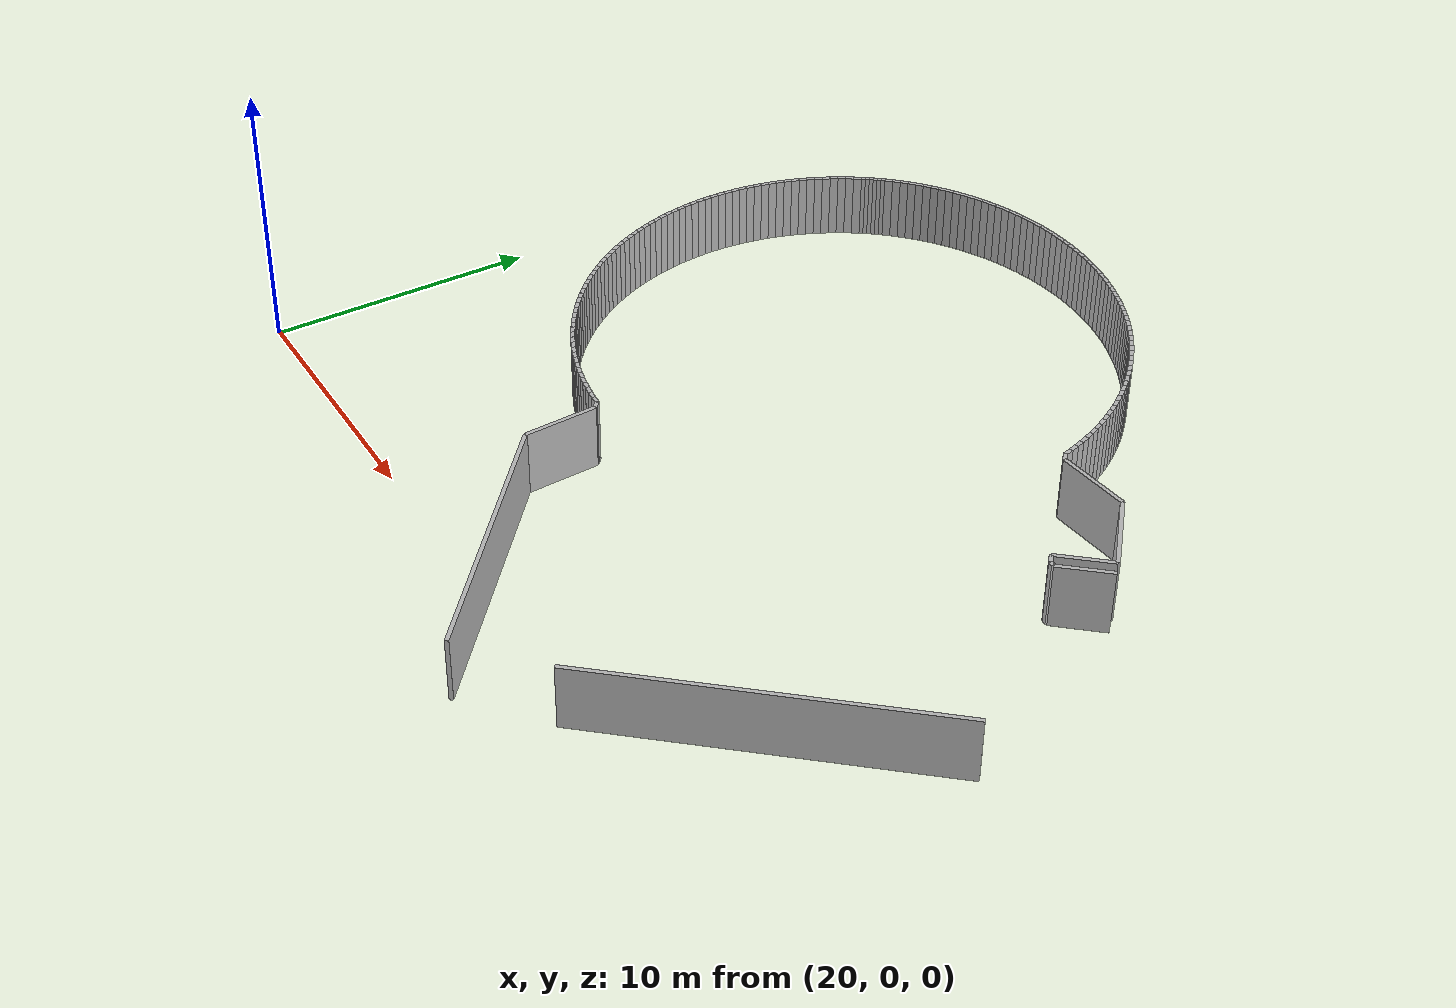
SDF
<?xml version="1.0" ?>
<sdf version="1.6">
  <model name="sps_4011">
    <pose frame="">0 0 0 0 -0 0</pose>
    <static>1</static>
    <self_collide>0</self_collide>
    <allow_auto_disable>0</allow_auto_disable>
    <link name="Wall1117">
      <kinematic>0</kinematic>
      <gravity>1</gravity>
      <self_collide>0</self_collide>
      <collision name="collision">
        <geometry>
          <box>
            <size>13.0009 0.15 2.5</size>
          </box>
        </geometry>
        <pose frame="">0 0 0 0 -0 0</pose>
      </collision>
      <visual name="visual">
        <geometry>
          <box>
            <size>13.0009 0.15 2.5</size>
          </box>
        </geometry>
        <pose frame="">0 0 0 0 -0 0</pose>
        <cast_shadows>1</cast_shadows>
        <transparency>0.0</transparency>
      </visual>
      <pose frame="">47.7584 4.36549 1.25 0 0 -2.27375</pose>
    </link>
    <link name="Wall1122">
      <kinematic>0</kinematic>
      <gravity>1</gravity>
      <self_collide>0</self_collide>
      <collision name="collision">
        <geometry>
          <box>
            <size>10.3999 0.15 2.5</size>
          </box>
        </geometry>
        <pose frame="">0 0 0 0 -0 0</pose>
      </collision>
      <visual name="visual">
        <geometry>
          <box>
            <size>10.3999 0.15 2.5</size>
          </box>
        </geometry>
        <pose frame="">0 0 0 0 -0 0</pose>
        <cast_shadows>1</cast_shadows>
        <transparency>0.0</transparency>
      </visual>
      <pose frame="">36.9448 0.420974 1.25 0 -0 2.43867</pose>
    </link>
    <link name="Wall1123">
      <kinematic>0</kinematic>
      <gravity>1</gravity>
      <self_collide>0</self_collide>
      <collision name="collision">
        <geometry>
          <box>
            <size>2.75904 0.15 2.5</size>
          </box>
        </geometry>
        <pose frame="">0 0 0 0 -0 0</pose>
      </collision>
      <visual name="visual">
        <geometry>
          <box>
            <size>2.75904 0.15 2.5</size>
          </box>
        </geometry>
        <pose frame="">0 0 0 0 -0 0</pose>
        <cast_shadows>1</cast_shadows>
        <transparency>0.0</transparency>
      </visual>
      <pose frame="">32.899 5.15977 1.25 0 -0 1.62766</pose>
    </link>
    <link name="Wall1124">
      <kinematic>0</kinematic>
      <gravity>1</gravity>
      <self_collide>0</self_collide>
      <collision name="collision">
        <geometry>
          <box>
            <size>0.299242 0.15 2.5</size>
          </box>
        </geometry>
        <pose frame="">0 0 0 0 -0 0</pose>
      </collision>
      <visual name="visual">
        <geometry>
          <box>
            <size>0.299242 0.15 2.5</size>
          </box>
        </geometry>
        <pose frame="">0 0 0 0 -0 0</pose>
        <cast_shadows>1</cast_shadows>
        <transparency>0.0</transparency>
      </visual>
      <pose frame="">32.7067 6.63399 1.25 0 -0 2.4369</pose>
    </link>
    <link name="Wall1125">
      <kinematic>0</kinematic>
      <gravity>1</gravity>
      <self_collide>0</self_collide>
      <collision name="collision">
        <geometry>
          <box>
            <size>0.304996 0.15 2.5</size>
          </box>
        </geometry>
        <pose frame="">0 0 0 0 -0 0</pose>
      </collision>
      <visual name="visual">
        <geometry>
          <box>
            <size>0.304996 0.15 2.5</size>
          </box>
        </geometry>
        <pose frame="">0 0 0 0 -0 0</pose>
        <cast_shadows>1</cast_shadows>
        <transparency>0.0</transparency>
      </visual>
      <pose frame="">32.4408 6.74422 1.25 0 -0 3.05423</pose>
    </link>
    <link name="Wall1126">
      <kinematic>0</kinematic>
      <gravity>1</gravity>
      <self_collide>0</self_collide>
      <collision name="collision">
        <geometry>
          <box>
            <size>0.304719 0.15 2.5</size>
          </box>
        </geometry>
        <pose frame="">0 0 0 0 -0 0</pose>
      </collision>
      <visual name="visual">
        <geometry>
          <box>
            <size>0.304719 0.15 2.5</size>
          </box>
        </geometry>
        <pose frame="">0 0 0 0 -0 0</pose>
        <cast_shadows>1</cast_shadows>
        <transparency>0.0</transparency>
      </visual>
      <pose frame="">32.1375 6.7754 1.25 0 -0 3.02395</pose>
    </link>
    <link name="Wall1127">
      <kinematic>0</kinematic>
      <gravity>1</gravity>
      <self_collide>0</self_collide>
      <collision name="collision">
        <geometry>
          <box>
            <size>0.304703 0.15 2.5</size>
          </box>
        </geometry>
        <pose frame="">0 0 0 0 -0 0</pose>
      </collision>
      <visual name="visual">
        <geometry>
          <box>
            <size>0.304703 0.15 2.5</size>
          </box>
        </geometry>
        <pose frame="">0 0 0 0 -0 0</pose>
        <cast_shadows>1</cast_shadows>
        <transparency>0.0</transparency>
      </visual>
      <pose frame="">31.8355 6.81569 1.25 0 -0 2.99403</pose>
    </link>
    <link name="Wall1128">
      <kinematic>0</kinematic>
      <gravity>1</gravity>
      <self_collide>0</self_collide>
      <collision name="collision">
        <geometry>
          <box>
            <size>0.304845 0.15 2.5</size>
          </box>
        </geometry>
        <pose frame="">0 0 0 0 -0 0</pose>
      </collision>
      <visual name="visual">
        <geometry>
          <box>
            <size>0.304845 0.15 2.5</size>
          </box>
        </geometry>
        <pose frame="">0 0 0 0 -0 0</pose>
        <cast_shadows>1</cast_shadows>
        <transparency>0.0</transparency>
      </visual>
      <pose frame="">31.5348 6.86519 1.25 0 -0 2.96285</pose>
    </link>
    <link name="Wall1129">
      <kinematic>0</kinematic>
      <gravity>1</gravity>
      <self_collide>0</self_collide>
      <collision name="collision">
        <geometry>
          <box>
            <size>0.304848 0.15 2.5</size>
          </box>
        </geometry>
        <pose frame="">0 0 0 0 -0 0</pose>
      </collision>
      <visual name="visual">
        <geometry>
          <box>
            <size>0.304848 0.15 2.5</size>
          </box>
        </geometry>
        <pose frame="">0 0 0 0 -0 0</pose>
        <cast_shadows>1</cast_shadows>
        <transparency>0.0</transparency>
      </visual>
      <pose frame="">31.2357 6.9239 1.25 0 -0 2.93265</pose>
    </link>
    <link name="Wall1130">
      <kinematic>0</kinematic>
      <gravity>1</gravity>
      <self_collide>0</self_collide>
      <collision name="collision">
        <geometry>
          <box>
            <size>0.304863 0.15 2.5</size>
          </box>
        </geometry>
        <pose frame="">0 0 0 0 -0 0</pose>
      </collision>
      <visual name="visual">
        <geometry>
          <box>
            <size>0.304863 0.15 2.5</size>
          </box>
        </geometry>
        <pose frame="">0 0 0 0 -0 0</pose>
        <cast_shadows>1</cast_shadows>
        <transparency>0.0</transparency>
      </visual>
      <pose frame="">30.9385 6.99159 1.25 0 -0 2.90268</pose>
    </link>
    <link name="Wall1131">
      <kinematic>0</kinematic>
      <gravity>1</gravity>
      <self_collide>0</self_collide>
      <collision name="collision">
        <geometry>
          <box>
            <size>0.304661 0.15 2.5</size>
          </box>
        </geometry>
        <pose frame="">0 0 0 0 -0 0</pose>
      </collision>
      <visual name="visual">
        <geometry>
          <box>
            <size>0.304661 0.15 2.5</size>
          </box>
        </geometry>
        <pose frame="">0 0 0 0 -0 0</pose>
        <cast_shadows>1</cast_shadows>
        <transparency>0.0</transparency>
      </visual>
      <pose frame="">30.6436 7.06837 1.25 0 -0 2.87105</pose>
    </link>
    <link name="Wall1132">
      <kinematic>0</kinematic>
      <gravity>1</gravity>
      <self_collide>0</self_collide>
      <collision name="collision">
        <geometry>
          <box>
            <size>0.304852 0.15 2.5</size>
          </box>
        </geometry>
        <pose frame="">0 0 0 0 -0 0</pose>
      </collision>
      <visual name="visual">
        <geometry>
          <box>
            <size>0.304852 0.15 2.5</size>
          </box>
        </geometry>
        <pose frame="">0 0 0 0 -0 0</pose>
        <cast_shadows>1</cast_shadows>
        <transparency>0.0</transparency>
      </visual>
      <pose frame="">30.3512 7.15419 1.25 0 -0 2.84118</pose>
    </link>
    <link name="Wall1133">
      <kinematic>0</kinematic>
      <gravity>1</gravity>
      <self_collide>0</self_collide>
      <collision name="collision">
        <geometry>
          <box>
            <size>0.304737 0.15 2.5</size>
          </box>
        </geometry>
        <pose frame="">0 0 0 0 -0 0</pose>
      </collision>
      <visual name="visual">
        <geometry>
          <box>
            <size>0.304737 0.15 2.5</size>
          </box>
        </geometry>
        <pose frame="">0 0 0 0 -0 0</pose>
        <cast_shadows>1</cast_shadows>
        <transparency>0.0</transparency>
      </visual>
      <pose frame="">30.0615 7.24879 1.25 0 -0 2.81072</pose>
    </link>
    <link name="Wall1134">
      <kinematic>0</kinematic>
      <gravity>1</gravity>
      <self_collide>0</self_collide>
      <collision name="collision">
        <geometry>
          <box>
            <size>0.304848 0.15 2.5</size>
          </box>
        </geometry>
        <pose frame="">0 0 0 0 -0 0</pose>
      </collision>
      <visual name="visual">
        <geometry>
          <box>
            <size>0.304848 0.15 2.5</size>
          </box>
        </geometry>
        <pose frame="">0 0 0 0 -0 0</pose>
        <cast_shadows>1</cast_shadows>
        <transparency>0.0</transparency>
      </visual>
      <pose frame="">29.7749 7.35219 1.25 0 -0 2.7802</pose>
    </link>
    <link name="Wall1135">
      <kinematic>0</kinematic>
      <gravity>1</gravity>
      <self_collide>0</self_collide>
      <collision name="collision">
        <geometry>
          <box>
            <size>0.304722 0.15 2.5</size>
          </box>
        </geometry>
        <pose frame="">0 0 0 0 -0 0</pose>
      </collision>
      <visual name="visual">
        <geometry>
          <box>
            <size>0.304722 0.15 2.5</size>
          </box>
        </geometry>
        <pose frame="">0 0 0 0 -0 0</pose>
        <cast_shadows>1</cast_shadows>
        <transparency>0.0</transparency>
      </visual>
      <pose frame="">29.4915 7.46428 1.25 0 -0 2.74967</pose>
    </link>
    <link name="Wall1136">
      <kinematic>0</kinematic>
      <gravity>1</gravity>
      <self_collide>0</self_collide>
      <collision name="collision">
        <geometry>
          <box>
            <size>0.304824 0.15 2.5</size>
          </box>
        </geometry>
        <pose frame="">0 0 0 0 -0 0</pose>
      </collision>
      <visual name="visual">
        <geometry>
          <box>
            <size>0.304824 0.15 2.5</size>
          </box>
        </geometry>
        <pose frame="">0 0 0 0 -0 0</pose>
        <cast_shadows>1</cast_shadows>
        <transparency>0.0</transparency>
      </visual>
      <pose frame="">29.2117 7.58498 1.25 0 -0 2.71906</pose>
    </link>
    <link name="Wall1137">
      <kinematic>0</kinematic>
      <gravity>1</gravity>
      <self_collide>0</self_collide>
      <collision name="collision">
        <geometry>
          <box>
            <size>0.304831 0.15 2.5</size>
          </box>
        </geometry>
        <pose frame="">0 0 0 0 -0 0</pose>
      </collision>
      <visual name="visual">
        <geometry>
          <box>
            <size>0.304831 0.15 2.5</size>
          </box>
        </geometry>
        <pose frame="">0 0 0 0 -0 0</pose>
        <cast_shadows>1</cast_shadows>
        <transparency>0.0</transparency>
      </visual>
      <pose frame="">28.9356 7.7141 1.25 0 -0 2.68923</pose>
    </link>
    <link name="Wall1138">
      <kinematic>0</kinematic>
      <gravity>1</gravity>
      <self_collide>0</self_collide>
      <collision name="collision">
        <geometry>
          <box>
            <size>0.304734 0.15 2.5</size>
          </box>
        </geometry>
        <pose frame="">0 0 0 0 -0 0</pose>
      </collision>
      <visual name="visual">
        <geometry>
          <box>
            <size>0.304734 0.15 2.5</size>
          </box>
        </geometry>
        <pose frame="">0 0 0 0 -0 0</pose>
        <cast_shadows>1</cast_shadows>
        <transparency>0.0</transparency>
      </visual>
      <pose frame="">28.6636 7.85152 1.25 0 -0 2.65833</pose>
    </link>
    <link name="Wall1139">
      <kinematic>0</kinematic>
      <gravity>1</gravity>
      <self_collide>0</self_collide>
      <collision name="collision">
        <geometry>
          <box>
            <size>0.304981 0.15 2.5</size>
          </box>
        </geometry>
        <pose frame="">0 0 0 0 -0 0</pose>
      </collision>
      <visual name="visual">
        <geometry>
          <box>
            <size>0.304981 0.15 2.5</size>
          </box>
        </geometry>
        <pose frame="">0 0 0 0 -0 0</pose>
        <cast_shadows>1</cast_shadows>
        <transparency>0.0</transparency>
      </visual>
      <pose frame="">28.3959 7.9973 1.25 0 -0 2.62754</pose>
    </link>
    <link name="Wall1140">
      <kinematic>0</kinematic>
      <gravity>1</gravity>
      <self_collide>0</self_collide>
      <collision name="collision">
        <geometry>
          <box>
            <size>0.304719 0.15 2.5</size>
          </box>
        </geometry>
        <pose frame="">0 0 0 0 -0 0</pose>
      </collision>
      <visual name="visual">
        <geometry>
          <box>
            <size>0.304719 0.15 2.5</size>
          </box>
        </geometry>
        <pose frame="">0 0 0 0 -0 0</pose>
        <cast_shadows>1</cast_shadows>
        <transparency>0.0</transparency>
      </visual>
      <pose frame="">28.1327 8.15108 1.25 0 -0 2.59805</pose>
    </link>
    <link name="Wall1141">
      <kinematic>0</kinematic>
      <gravity>1</gravity>
      <self_collide>0</self_collide>
      <collision name="collision">
        <geometry>
          <box>
            <size>0.304849 0.15 2.5</size>
          </box>
        </geometry>
        <pose frame="">0 0 0 0 -0 0</pose>
      </collision>
      <visual name="visual">
        <geometry>
          <box>
            <size>0.304849 0.15 2.5</size>
          </box>
        </geometry>
        <pose frame="">0 0 0 0 -0 0</pose>
        <cast_shadows>1</cast_shadows>
        <transparency>0.0</transparency>
      </visual>
      <pose frame="">27.8744 8.31279 1.25 0 -0 2.56642</pose>
    </link>
    <link name="Wall1142">
      <kinematic>0</kinematic>
      <gravity>1</gravity>
      <self_collide>0</self_collide>
      <collision name="collision">
        <geometry>
          <box>
            <size>0.304751 0.15 2.5</size>
          </box>
        </geometry>
        <pose frame="">0 0 0 0 -0 0</pose>
      </collision>
      <visual name="visual">
        <geometry>
          <box>
            <size>0.304751 0.15 2.5</size>
          </box>
        </geometry>
        <pose frame="">0 0 0 0 -0 0</pose>
        <cast_shadows>1</cast_shadows>
        <transparency>0.0</transparency>
      </visual>
      <pose frame="">27.6212 8.48241 1.25 0 -0 2.53631</pose>
    </link>
    <link name="Wall1143">
      <kinematic>0</kinematic>
      <gravity>1</gravity>
      <self_collide>0</self_collide>
      <collision name="collision">
        <geometry>
          <box>
            <size>0.304782 0.15 2.5</size>
          </box>
        </geometry>
        <pose frame="">0 0 0 0 -0 0</pose>
      </collision>
      <visual name="visual">
        <geometry>
          <box>
            <size>0.304782 0.15 2.5</size>
          </box>
        </geometry>
        <pose frame="">0 0 0 0 -0 0</pose>
        <cast_shadows>1</cast_shadows>
        <transparency>0.0</transparency>
      </visual>
      <pose frame="">27.3733 8.65959 1.25 0 -0 2.50586</pose>
    </link>
    <link name="Wall1144">
      <kinematic>0</kinematic>
      <gravity>1</gravity>
      <self_collide>0</self_collide>
      <collision name="collision">
        <geometry>
          <box>
            <size>0.30478 0.15 2.5</size>
          </box>
        </geometry>
        <pose frame="">0 0 0 0 -0 0</pose>
      </collision>
      <visual name="visual">
        <geometry>
          <box>
            <size>0.30478 0.15 2.5</size>
          </box>
        </geometry>
        <pose frame="">0 0 0 0 -0 0</pose>
        <cast_shadows>1</cast_shadows>
        <transparency>0.0</transparency>
      </visual>
      <pose frame="">27.1309 8.84428 1.25 0 -0 2.47514</pose>
    </link>
    <link name="Wall1145">
      <kinematic>0</kinematic>
      <gravity>1</gravity>
      <self_collide>0</self_collide>
      <collision name="collision">
        <geometry>
          <box>
            <size>0.304862 0.15 2.5</size>
          </box>
        </geometry>
        <pose frame="">0 0 0 0 -0 0</pose>
      </collision>
      <visual name="visual">
        <geometry>
          <box>
            <size>0.304862 0.15 2.5</size>
          </box>
        </geometry>
        <pose frame="">0 0 0 0 -0 0</pose>
        <cast_shadows>1</cast_shadows>
        <transparency>0.0</transparency>
      </visual>
      <pose frame="">26.8942 9.0363 1.25 0 -0 2.44493</pose>
    </link>
    <link name="Wall1146">
      <kinematic>0</kinematic>
      <gravity>1</gravity>
      <self_collide>0</self_collide>
      <collision name="collision">
        <geometry>
          <box>
            <size>0.304831 0.15 2.5</size>
          </box>
        </geometry>
        <pose frame="">0 0 0 0 -0 0</pose>
      </collision>
      <visual name="visual">
        <geometry>
          <box>
            <size>0.304831 0.15 2.5</size>
          </box>
        </geometry>
        <pose frame="">0 0 0 0 -0 0</pose>
        <cast_shadows>1</cast_shadows>
        <transparency>0.0</transparency>
      </visual>
      <pose frame="">26.6634 9.2354 1.25 0 -0 2.4147</pose>
    </link>
    <link name="Wall1147">
      <kinematic>0</kinematic>
      <gravity>1</gravity>
      <self_collide>0</self_collide>
      <collision name="collision">
        <geometry>
          <box>
            <size>0.304729 0.15 2.5</size>
          </box>
        </geometry>
        <pose frame="">0 0 0 0 -0 0</pose>
      </collision>
      <visual name="visual">
        <geometry>
          <box>
            <size>0.304729 0.15 2.5</size>
          </box>
        </geometry>
        <pose frame="">0 0 0 0 -0 0</pose>
        <cast_shadows>1</cast_shadows>
        <transparency>0.0</transparency>
      </visual>
      <pose frame="">26.4388 9.44139 1.25 0 -0 2.38396</pose>
    </link>
    <link name="Wall1148">
      <kinematic>0</kinematic>
      <gravity>1</gravity>
      <self_collide>0</self_collide>
      <collision name="collision">
        <geometry>
          <box>
            <size>0.304656 0.15 2.5</size>
          </box>
        </geometry>
        <pose frame="">0 0 0 0 -0 0</pose>
      </collision>
      <visual name="visual">
        <geometry>
          <box>
            <size>0.304656 0.15 2.5</size>
          </box>
        </geometry>
        <pose frame="">0 0 0 0 -0 0</pose>
        <cast_shadows>1</cast_shadows>
        <transparency>0.0</transparency>
      </visual>
      <pose frame="">26.2207 9.6541 1.25 0 -0 2.3535</pose>
    </link>
    <link name="Wall1149">
      <kinematic>0</kinematic>
      <gravity>1</gravity>
      <self_collide>0</self_collide>
      <collision name="collision">
        <geometry>
          <box>
            <size>0.304907 0.15 2.5</size>
          </box>
        </geometry>
        <pose frame="">0 0 0 0 -0 0</pose>
      </collision>
      <visual name="visual">
        <geometry>
          <box>
            <size>0.304907 0.15 2.5</size>
          </box>
        </geometry>
        <pose frame="">0 0 0 0 -0 0</pose>
        <cast_shadows>1</cast_shadows>
        <transparency>0.0</transparency>
      </visual>
      <pose frame="">26.0091 9.8734 1.25 0 -0 2.32321</pose>
    </link>
    <link name="Wall1150">
      <kinematic>0</kinematic>
      <gravity>1</gravity>
      <self_collide>0</self_collide>
      <collision name="collision">
        <geometry>
          <box>
            <size>0.30484 0.15 2.5</size>
          </box>
        </geometry>
        <pose frame="">0 0 0 0 -0 0</pose>
      </collision>
      <visual name="visual">
        <geometry>
          <box>
            <size>0.30484 0.15 2.5</size>
          </box>
        </geometry>
        <pose frame="">0 0 0 0 -0 0</pose>
        <cast_shadows>1</cast_shadows>
        <transparency>0.0</transparency>
      </visual>
      <pose frame="">25.8042 10.0991 1.25 0 -0 2.29258</pose>
    </link>
    <link name="Wall1151">
      <kinematic>0</kinematic>
      <gravity>1</gravity>
      <self_collide>0</self_collide>
      <collision name="collision">
        <geometry>
          <box>
            <size>0.304715 0.15 2.5</size>
          </box>
        </geometry>
        <pose frame="">0 0 0 0 -0 0</pose>
      </collision>
      <visual name="visual">
        <geometry>
          <box>
            <size>0.304715 0.15 2.5</size>
          </box>
        </geometry>
        <pose frame="">0 0 0 0 -0 0</pose>
        <cast_shadows>1</cast_shadows>
        <transparency>0.0</transparency>
      </visual>
      <pose frame="">25.6063 10.3309 1.25 0 -0 2.26187</pose>
    </link>
    <link name="Wall1152">
      <kinematic>0</kinematic>
      <gravity>1</gravity>
      <self_collide>0</self_collide>
      <collision name="collision">
        <geometry>
          <box>
            <size>0.304845 0.15 2.5</size>
          </box>
        </geometry>
        <pose frame="">0 0 0 0 -0 0</pose>
      </collision>
      <visual name="visual">
        <geometry>
          <box>
            <size>0.304845 0.15 2.5</size>
          </box>
        </geometry>
        <pose frame="">0 0 0 0 -0 0</pose>
        <cast_shadows>1</cast_shadows>
        <transparency>0.0</transparency>
      </visual>
      <pose frame="">25.4156 10.5686 1.25 0 -0 2.232</pose>
    </link>
    <link name="Wall1153">
      <kinematic>0</kinematic>
      <gravity>1</gravity>
      <self_collide>0</self_collide>
      <collision name="collision">
        <geometry>
          <box>
            <size>0.30469 0.15 2.5</size>
          </box>
        </geometry>
        <pose frame="">0 0 0 0 -0 0</pose>
      </collision>
      <visual name="visual">
        <geometry>
          <box>
            <size>0.30469 0.15 2.5</size>
          </box>
        </geometry>
        <pose frame="">0 0 0 0 -0 0</pose>
        <cast_shadows>1</cast_shadows>
        <transparency>0.0</transparency>
      </visual>
      <pose frame="">25.2323 10.812 1.25 0 -0 2.20104</pose>
    </link>
    <link name="Wall1154">
      <kinematic>0</kinematic>
      <gravity>1</gravity>
      <self_collide>0</self_collide>
      <collision name="collision">
        <geometry>
          <box>
            <size>0.304962 0.15 2.5</size>
          </box>
        </geometry>
        <pose frame="">0 0 0 0 -0 0</pose>
      </collision>
      <visual name="visual">
        <geometry>
          <box>
            <size>0.304962 0.15 2.5</size>
          </box>
        </geometry>
        <pose frame="">0 0 0 0 -0 0</pose>
        <cast_shadows>1</cast_shadows>
        <transparency>0.0</transparency>
      </visual>
      <pose frame="">25.0565 11.061 1.25 0 -0 2.17001</pose>
    </link>
    <link name="Wall1155">
      <kinematic>0</kinematic>
      <gravity>1</gravity>
      <self_collide>0</self_collide>
      <collision name="collision">
        <geometry>
          <box>
            <size>0.304756 0.15 2.5</size>
          </box>
        </geometry>
        <pose frame="">0 0 0 0 -0 0</pose>
      </collision>
      <visual name="visual">
        <geometry>
          <box>
            <size>0.304756 0.15 2.5</size>
          </box>
        </geometry>
        <pose frame="">0 0 0 0 -0 0</pose>
        <cast_shadows>1</cast_shadows>
        <transparency>0.0</transparency>
      </visual>
      <pose frame="">24.8883 11.3152 1.25 0 -0 2.14069</pose>
    </link>
    <link name="Wall1156">
      <kinematic>0</kinematic>
      <gravity>1</gravity>
      <self_collide>0</self_collide>
      <collision name="collision">
        <geometry>
          <box>
            <size>0.304529 0.15 2.5</size>
          </box>
        </geometry>
        <pose frame="">0 0 0 0 -0 0</pose>
      </collision>
      <visual name="visual">
        <geometry>
          <box>
            <size>0.304529 0.15 2.5</size>
          </box>
        </geometry>
        <pose frame="">0 0 0 0 -0 0</pose>
        <cast_shadows>1</cast_shadows>
        <transparency>0.0</transparency>
      </visual>
      <pose frame="">24.7277 11.5741 1.25 0 -0 2.11098</pose>
    </link>
    <link name="Wall1157">
      <kinematic>0</kinematic>
      <gravity>1</gravity>
      <self_collide>0</self_collide>
      <collision name="collision">
        <geometry>
          <box>
            <size>0.304861 0.15 2.5</size>
          </box>
        </geometry>
        <pose frame="">0 0 0 0 -0 0</pose>
      </collision>
      <visual name="visual">
        <geometry>
          <box>
            <size>0.304861 0.15 2.5</size>
          </box>
        </geometry>
        <pose frame="">0 0 0 0 -0 0</pose>
        <cast_shadows>1</cast_shadows>
        <transparency>0.0</transparency>
      </visual>
      <pose frame="">24.5753 11.8379 1.25 0 -0 2.07842</pose>
    </link>
    <link name="Wall1158">
      <kinematic>0</kinematic>
      <gravity>1</gravity>
      <self_collide>0</self_collide>
      <collision name="collision">
        <geometry>
          <box>
            <size>0.304788 0.15 2.5</size>
          </box>
        </geometry>
        <pose frame="">0 0 0 0 -0 0</pose>
      </collision>
      <visual name="visual">
        <geometry>
          <box>
            <size>0.304788 0.15 2.5</size>
          </box>
        </geometry>
        <pose frame="">0 0 0 0 -0 0</pose>
        <cast_shadows>1</cast_shadows>
        <transparency>0.0</transparency>
      </visual>
      <pose frame="">24.4311 12.1064 1.25 0 -0 2.04877</pose>
    </link>
    <link name="Wall1159">
      <kinematic>0</kinematic>
      <gravity>1</gravity>
      <self_collide>0</self_collide>
      <collision name="collision">
        <geometry>
          <box>
            <size>0.305015 0.15 2.5</size>
          </box>
        </geometry>
        <pose frame="">0 0 0 0 -0 0</pose>
      </collision>
      <visual name="visual">
        <geometry>
          <box>
            <size>0.305015 0.15 2.5</size>
          </box>
        </geometry>
        <pose frame="">0 0 0 0 -0 0</pose>
        <cast_shadows>1</cast_shadows>
        <transparency>0.0</transparency>
      </visual>
      <pose frame="">24.295 12.3792 1.25 0 -0 2.01842</pose>
    </link>
    <link name="Wall1160">
      <kinematic>0</kinematic>
      <gravity>1</gravity>
      <self_collide>0</self_collide>
      <collision name="collision">
        <geometry>
          <box>
            <size>0.304635 0.15 2.5</size>
          </box>
        </geometry>
        <pose frame="">0 0 0 0 -0 0</pose>
      </collision>
      <visual name="visual">
        <geometry>
          <box>
            <size>0.304635 0.15 2.5</size>
          </box>
        </geometry>
        <pose frame="">0 0 0 0 -0 0</pose>
        <cast_shadows>1</cast_shadows>
        <transparency>0.0</transparency>
      </visual>
      <pose frame="">24.1674 12.656 1.25 0 -0 1.98703</pose>
    </link>
    <link name="Wall1161">
      <kinematic>0</kinematic>
      <gravity>1</gravity>
      <self_collide>0</self_collide>
      <collision name="collision">
        <geometry>
          <box>
            <size>0.304923 0.15 2.5</size>
          </box>
        </geometry>
        <pose frame="">0 0 0 0 -0 0</pose>
      </collision>
      <visual name="visual">
        <geometry>
          <box>
            <size>0.304923 0.15 2.5</size>
          </box>
        </geometry>
        <pose frame="">0 0 0 0 -0 0</pose>
        <cast_shadows>1</cast_shadows>
        <transparency>0.0</transparency>
      </visual>
      <pose frame="">24.0484 12.9365 1.25 0 -0 1.95747</pose>
    </link>
    <link name="Wall1162">
      <kinematic>0</kinematic>
      <gravity>1</gravity>
      <self_collide>0</self_collide>
      <collision name="collision">
        <geometry>
          <box>
            <size>0.304691 0.15 2.5</size>
          </box>
        </geometry>
        <pose frame="">0 0 0 0 -0 0</pose>
      </collision>
      <visual name="visual">
        <geometry>
          <box>
            <size>0.304691 0.15 2.5</size>
          </box>
        </geometry>
        <pose frame="">0 0 0 0 -0 0</pose>
        <cast_shadows>1</cast_shadows>
        <transparency>0.0</transparency>
      </visual>
      <pose frame="">23.9378 13.2205 1.25 0 -0 1.92682</pose>
    </link>
    <link name="Wall1163">
      <kinematic>0</kinematic>
      <gravity>1</gravity>
      <self_collide>0</self_collide>
      <collision name="collision">
        <geometry>
          <box>
            <size>0.304862 0.15 2.5</size>
          </box>
        </geometry>
        <pose frame="">0 0 0 0 -0 0</pose>
      </collision>
      <visual name="visual">
        <geometry>
          <box>
            <size>0.304862 0.15 2.5</size>
          </box>
        </geometry>
        <pose frame="">0 0 0 0 -0 0</pose>
        <cast_shadows>1</cast_shadows>
        <transparency>0.0</transparency>
      </visual>
      <pose frame="">23.8359 13.5077 1.25 0 -0 1.89666</pose>
    </link>
    <link name="Wall1164">
      <kinematic>0</kinematic>
      <gravity>1</gravity>
      <self_collide>0</self_collide>
      <collision name="collision">
        <geometry>
          <box>
            <size>0.304736 0.15 2.5</size>
          </box>
        </geometry>
        <pose frame="">0 0 0 0 -0 0</pose>
      </collision>
      <visual name="visual">
        <geometry>
          <box>
            <size>0.304736 0.15 2.5</size>
          </box>
        </geometry>
        <pose frame="">0 0 0 0 -0 0</pose>
        <cast_shadows>1</cast_shadows>
        <transparency>0.0</transparency>
      </visual>
      <pose frame="">23.7428 13.7979 1.25 0 -0 1.86588</pose>
    </link>
    <link name="Wall1165">
      <kinematic>0</kinematic>
      <gravity>1</gravity>
      <self_collide>0</self_collide>
      <collision name="collision">
        <geometry>
          <box>
            <size>0.304813 0.15 2.5</size>
          </box>
        </geometry>
        <pose frame="">0 0 0 0 -0 0</pose>
      </collision>
      <visual name="visual">
        <geometry>
          <box>
            <size>0.304813 0.15 2.5</size>
          </box>
        </geometry>
        <pose frame="">0 0 0 0 -0 0</pose>
        <cast_shadows>1</cast_shadows>
        <transparency>0.0</transparency>
      </visual>
      <pose frame="">23.6586 14.0908 1.25 0 -0 1.83559</pose>
    </link>
    <link name="Wall1166">
      <kinematic>0</kinematic>
      <gravity>1</gravity>
      <self_collide>0</self_collide>
      <collision name="collision">
        <geometry>
          <box>
            <size>0.3047 0.15 2.5</size>
          </box>
        </geometry>
        <pose frame="">0 0 0 0 -0 0</pose>
      </collision>
      <visual name="visual">
        <geometry>
          <box>
            <size>0.3047 0.15 2.5</size>
          </box>
        </geometry>
        <pose frame="">0 0 0 0 -0 0</pose>
        <cast_shadows>1</cast_shadows>
        <transparency>0.0</transparency>
      </visual>
      <pose frame="">23.5835 14.3861 1.25 0 -0 1.80407</pose>
    </link>
    <link name="Wall1167">
      <kinematic>0</kinematic>
      <gravity>1</gravity>
      <self_collide>0</self_collide>
      <collision name="collision">
        <geometry>
          <box>
            <size>0.304906 0.15 2.5</size>
          </box>
        </geometry>
        <pose frame="">0 0 0 0 -0 0</pose>
      </collision>
      <visual name="visual">
        <geometry>
          <box>
            <size>0.304906 0.15 2.5</size>
          </box>
        </geometry>
        <pose frame="">0 0 0 0 -0 0</pose>
        <cast_shadows>1</cast_shadows>
        <transparency>0.0</transparency>
      </visual>
      <pose frame="">23.5174 14.6836 1.25 0 -0 1.77479</pose>
    </link>
    <link name="Wall1168">
      <kinematic>0</kinematic>
      <gravity>1</gravity>
      <self_collide>0</self_collide>
      <collision name="collision">
        <geometry>
          <box>
            <size>0.304715 0.15 2.5</size>
          </box>
        </geometry>
        <pose frame="">0 0 0 0 -0 0</pose>
      </collision>
      <visual name="visual">
        <geometry>
          <box>
            <size>0.304715 0.15 2.5</size>
          </box>
        </geometry>
        <pose frame="">0 0 0 0 -0 0</pose>
        <cast_shadows>1</cast_shadows>
        <transparency>0.0</transparency>
      </visual>
      <pose frame="">23.4603 14.983 1.25 0 -0 1.74372</pose>
    </link>
    <link name="Wall1169">
      <kinematic>0</kinematic>
      <gravity>1</gravity>
      <self_collide>0</self_collide>
      <collision name="collision">
        <geometry>
          <box>
            <size>0.304897 0.15 2.5</size>
          </box>
        </geometry>
        <pose frame="">0 0 0 0 -0 0</pose>
      </collision>
      <visual name="visual">
        <geometry>
          <box>
            <size>0.304897 0.15 2.5</size>
          </box>
        </geometry>
        <pose frame="">0 0 0 0 -0 0</pose>
        <cast_shadows>1</cast_shadows>
        <transparency>0.0</transparency>
      </visual>
      <pose frame="">23.4124 15.284 1.25 0 -0 1.713</pose>
    </link>
    <link name="Wall1170">
      <kinematic>0</kinematic>
      <gravity>1</gravity>
      <self_collide>0</self_collide>
      <collision name="collision">
        <geometry>
          <box>
            <size>0.304739 0.15 2.5</size>
          </box>
        </geometry>
        <pose frame="">0 0 0 0 -0 0</pose>
      </collision>
      <visual name="visual">
        <geometry>
          <box>
            <size>0.304739 0.15 2.5</size>
          </box>
        </geometry>
        <pose frame="">0 0 0 0 -0 0</pose>
        <cast_shadows>1</cast_shadows>
        <transparency>0.0</transparency>
      </visual>
      <pose frame="">23.3736 15.5863 1.25 0 -0 1.6838</pose>
    </link>
    <link name="Wall1171">
      <kinematic>0</kinematic>
      <gravity>1</gravity>
      <self_collide>0</self_collide>
      <collision name="collision">
        <geometry>
          <box>
            <size>0.304847 0.15 2.5</size>
          </box>
        </geometry>
        <pose frame="">0 0 0 0 -0 0</pose>
      </collision>
      <visual name="visual">
        <geometry>
          <box>
            <size>0.304847 0.15 2.5</size>
          </box>
        </geometry>
        <pose frame="">0 0 0 0 -0 0</pose>
        <cast_shadows>1</cast_shadows>
        <transparency>0.0</transparency>
      </visual>
      <pose frame="">23.344 15.8896 1.25 0 -0 1.65237</pose>
    </link>
    <link name="Wall1172">
      <kinematic>0</kinematic>
      <gravity>1</gravity>
      <self_collide>0</self_collide>
      <collision name="collision">
        <geometry>
          <box>
            <size>0.30478 0.15 2.5</size>
          </box>
        </geometry>
        <pose frame="">0 0 0 0 -0 0</pose>
      </collision>
      <visual name="visual">
        <geometry>
          <box>
            <size>0.30478 0.15 2.5</size>
          </box>
        </geometry>
        <pose frame="">0 0 0 0 -0 0</pose>
        <cast_shadows>1</cast_shadows>
        <transparency>0.0</transparency>
      </visual>
      <pose frame="">23.3238 16.1937 1.25 0 -0 1.62188</pose>
    </link>
    <link name="Wall1173">
      <kinematic>0</kinematic>
      <gravity>1</gravity>
      <self_collide>0</self_collide>
      <collision name="collision">
        <geometry>
          <box>
            <size>0.304629 0.15 2.5</size>
          </box>
        </geometry>
        <pose frame="">0 0 0 0 -0 0</pose>
      </collision>
      <visual name="visual">
        <geometry>
          <box>
            <size>0.304629 0.15 2.5</size>
          </box>
        </geometry>
        <pose frame="">0 0 0 0 -0 0</pose>
        <cast_shadows>1</cast_shadows>
        <transparency>0.0</transparency>
      </visual>
      <pose frame="">23.3129 16.4982 1.25 0 -0 1.59123</pose>
    </link>
    <link name="Wall1174">
      <kinematic>0</kinematic>
      <gravity>1</gravity>
      <self_collide>0</self_collide>
      <collision name="collision">
        <geometry>
          <box>
            <size>0.304823 0.15 2.5</size>
          </box>
        </geometry>
        <pose frame="">0 0 0 0 -0 0</pose>
      </collision>
      <visual name="visual">
        <geometry>
          <box>
            <size>0.304823 0.15 2.5</size>
          </box>
        </geometry>
        <pose frame="">0 0 0 0 -0 0</pose>
        <cast_shadows>1</cast_shadows>
        <transparency>0.0</transparency>
      </visual>
      <pose frame="">23.3112 16.8029 1.25 0 -0 1.56159</pose>
    </link>
    <link name="Wall1175">
      <kinematic>0</kinematic>
      <gravity>1</gravity>
      <self_collide>0</self_collide>
      <collision name="collision">
        <geometry>
          <box>
            <size>0.304878 0.15 2.5</size>
          </box>
        </geometry>
        <pose frame="">0 0 0 0 -0 0</pose>
      </collision>
      <visual name="visual">
        <geometry>
          <box>
            <size>0.304878 0.15 2.5</size>
          </box>
        </geometry>
        <pose frame="">0 0 0 0 -0 0</pose>
        <cast_shadows>1</cast_shadows>
        <transparency>0.0</transparency>
      </visual>
      <pose frame="">23.3188 17.1076 1.25 0 -0 1.53015</pose>
    </link>
    <link name="Wall1176">
      <kinematic>0</kinematic>
      <gravity>1</gravity>
      <self_collide>0</self_collide>
      <collision name="collision">
        <geometry>
          <box>
            <size>0.304783 0.15 2.5</size>
          </box>
        </geometry>
        <pose frame="">0 0 0 0 -0 0</pose>
      </collision>
      <visual name="visual">
        <geometry>
          <box>
            <size>0.304783 0.15 2.5</size>
          </box>
        </geometry>
        <pose frame="">0 0 0 0 -0 0</pose>
        <cast_shadows>1</cast_shadows>
        <transparency>0.0</transparency>
      </visual>
      <pose frame="">23.3358 17.4119 1.25 0 -0 1.49985</pose>
    </link>
    <link name="Wall1177">
      <kinematic>0</kinematic>
      <gravity>1</gravity>
      <self_collide>0</self_collide>
      <collision name="collision">
        <geometry>
          <box>
            <size>0.304706 0.15 2.5</size>
          </box>
        </geometry>
        <pose frame="">0 0 0 0 -0 0</pose>
      </collision>
      <visual name="visual">
        <geometry>
          <box>
            <size>0.304706 0.15 2.5</size>
          </box>
        </geometry>
        <pose frame="">0 0 0 0 -0 0</pose>
        <cast_shadows>1</cast_shadows>
        <transparency>0.0</transparency>
      </visual>
      <pose frame="">23.362 17.7155 1.25 0 -0 1.47007</pose>
    </link>
    <link name="Wall1178">
      <kinematic>0</kinematic>
      <gravity>1</gravity>
      <self_collide>0</self_collide>
      <collision name="collision">
        <geometry>
          <box>
            <size>0.304842 0.15 2.5</size>
          </box>
        </geometry>
        <pose frame="">0 0 0 0 -0 0</pose>
      </collision>
      <visual name="visual">
        <geometry>
          <box>
            <size>0.304842 0.15 2.5</size>
          </box>
        </geometry>
        <pose frame="">0 0 0 0 -0 0</pose>
        <cast_shadows>1</cast_shadows>
        <transparency>0.0</transparency>
      </visual>
      <pose frame="">23.3974 18.0182 1.25 0 -0 1.43867</pose>
    </link>
    <link name="Wall1179">
      <kinematic>0</kinematic>
      <gravity>1</gravity>
      <self_collide>0</self_collide>
      <collision name="collision">
        <geometry>
          <box>
            <size>0.304838 0.15 2.5</size>
          </box>
        </geometry>
        <pose frame="">0 0 0 0 -0 0</pose>
      </collision>
      <visual name="visual">
        <geometry>
          <box>
            <size>0.304838 0.15 2.5</size>
          </box>
        </geometry>
        <pose frame="">0 0 0 0 -0 0</pose>
        <cast_shadows>1</cast_shadows>
        <transparency>0.0</transparency>
      </visual>
      <pose frame="">23.442 18.3197 1.25 0 -0 1.40871</pose>
    </link>
    <link name="Wall1180">
      <kinematic>0</kinematic>
      <gravity>1</gravity>
      <self_collide>0</self_collide>
      <collision name="collision">
        <geometry>
          <box>
            <size>0.304808 0.15 2.5</size>
          </box>
        </geometry>
        <pose frame="">0 0 0 0 -0 0</pose>
      </collision>
      <visual name="visual">
        <geometry>
          <box>
            <size>0.304808 0.15 2.5</size>
          </box>
        </geometry>
        <pose frame="">0 0 0 0 -0 0</pose>
        <cast_shadows>1</cast_shadows>
        <transparency>0.0</transparency>
      </visual>
      <pose frame="">23.4957 18.6197 1.25 0 -0 1.37858</pose>
    </link>
    <link name="Wall1181">
      <kinematic>0</kinematic>
      <gravity>1</gravity>
      <self_collide>0</self_collide>
      <collision name="collision">
        <geometry>
          <box>
            <size>0.304764 0.15 2.5</size>
          </box>
        </geometry>
        <pose frame="">0 0 0 0 -0 0</pose>
      </collision>
      <visual name="visual">
        <geometry>
          <box>
            <size>0.304764 0.15 2.5</size>
          </box>
        </geometry>
        <pose frame="">0 0 0 0 -0 0</pose>
        <cast_shadows>1</cast_shadows>
        <transparency>0.0</transparency>
      </visual>
      <pose frame="">23.5586 18.9179 1.25 0 -0 1.34724</pose>
    </link>
    <link name="Wall1182">
      <kinematic>0</kinematic>
      <gravity>1</gravity>
      <self_collide>0</self_collide>
      <collision name="collision">
        <geometry>
          <box>
            <size>0.30472 0.15 2.5</size>
          </box>
        </geometry>
        <pose frame="">0 0 0 0 -0 0</pose>
      </collision>
      <visual name="visual">
        <geometry>
          <box>
            <size>0.30472 0.15 2.5</size>
          </box>
        </geometry>
        <pose frame="">0 0 0 0 -0 0</pose>
        <cast_shadows>1</cast_shadows>
        <transparency>0.0</transparency>
      </visual>
      <pose frame="">23.6306 19.214 1.25 0 -0 1.31732</pose>
    </link>
    <link name="Wall1183">
      <kinematic>0</kinematic>
      <gravity>1</gravity>
      <self_collide>0</self_collide>
      <collision name="collision">
        <geometry>
          <box>
            <size>0.304807 0.15 2.5</size>
          </box>
        </geometry>
        <pose frame="">0 0 0 0 -0 0</pose>
      </collision>
      <visual name="visual">
        <geometry>
          <box>
            <size>0.304807 0.15 2.5</size>
          </box>
        </geometry>
        <pose frame="">0 0 0 0 -0 0</pose>
        <cast_shadows>1</cast_shadows>
        <transparency>0.0</transparency>
      </visual>
      <pose frame="">23.7115 19.5078 1.25 0 -0 1.28686</pose>
    </link>
    <link name="Wall1184">
      <kinematic>0</kinematic>
      <gravity>1</gravity>
      <self_collide>0</self_collide>
      <collision name="collision">
        <geometry>
          <box>
            <size>0.304847 0.15 2.5</size>
          </box>
        </geometry>
        <pose frame="">0 0 0 0 -0 0</pose>
      </collision>
      <visual name="visual">
        <geometry>
          <box>
            <size>0.304847 0.15 2.5</size>
          </box>
        </geometry>
        <pose frame="">0 0 0 0 -0 0</pose>
        <cast_shadows>1</cast_shadows>
        <transparency>0.0</transparency>
      </visual>
      <pose frame="">23.8014 19.799 1.25 0 -0 1.25588</pose>
    </link>
    <link name="Wall1185">
      <kinematic>0</kinematic>
      <gravity>1</gravity>
      <self_collide>0</self_collide>
      <collision name="collision">
        <geometry>
          <box>
            <size>0.304752 0.15 2.5</size>
          </box>
        </geometry>
        <pose frame="">0 0 0 0 -0 0</pose>
      </collision>
      <visual name="visual">
        <geometry>
          <box>
            <size>0.304752 0.15 2.5</size>
          </box>
        </geometry>
        <pose frame="">0 0 0 0 -0 0</pose>
        <cast_shadows>1</cast_shadows>
        <transparency>0.0</transparency>
      </visual>
      <pose frame="">23.9003 20.0873 1.25 0 -0 1.22529</pose>
    </link>
    <link name="Wall1186">
      <kinematic>0</kinematic>
      <gravity>1</gravity>
      <self_collide>0</self_collide>
      <collision name="collision">
        <geometry>
          <box>
            <size>0.305046 0.15 2.5</size>
          </box>
        </geometry>
        <pose frame="">0 0 0 0 -0 0</pose>
      </collision>
      <visual name="visual">
        <geometry>
          <box>
            <size>0.305046 0.15 2.5</size>
          </box>
        </geometry>
        <pose frame="">0 0 0 0 -0 0</pose>
        <cast_shadows>1</cast_shadows>
        <transparency>0.0</transparency>
      </visual>
      <pose frame="">24.0078 20.3726 1.25 0 -0 1.19549</pose>
    </link>
    <link name="Wall1187">
      <kinematic>0</kinematic>
      <gravity>1</gravity>
      <self_collide>0</self_collide>
      <collision name="collision">
        <geometry>
          <box>
            <size>0.3048 0.15 2.5</size>
          </box>
        </geometry>
        <pose frame="">0 0 0 0 -0 0</pose>
      </collision>
      <visual name="visual">
        <geometry>
          <box>
            <size>0.3048 0.15 2.5</size>
          </box>
        </geometry>
        <pose frame="">0 0 0 0 -0 0</pose>
        <cast_shadows>1</cast_shadows>
        <transparency>0.0</transparency>
      </visual>
      <pose frame="">24.1239 20.6545 1.25 0 -0 1.16485</pose>
    </link>
    <link name="Wall1188">
      <kinematic>0</kinematic>
      <gravity>1</gravity>
      <self_collide>0</self_collide>
      <collision name="collision">
        <geometry>
          <box>
            <size>0.304734 0.15 2.5</size>
          </box>
        </geometry>
        <pose frame="">0 0 0 0 -0 0</pose>
      </collision>
      <visual name="visual">
        <geometry>
          <box>
            <size>0.304734 0.15 2.5</size>
          </box>
        </geometry>
        <pose frame="">0 0 0 0 -0 0</pose>
        <cast_shadows>1</cast_shadows>
        <transparency>0.0</transparency>
      </visual>
      <pose frame="">24.2484 20.9326 1.25 0 -0 1.13447</pose>
    </link>
    <link name="Wall1189">
      <kinematic>0</kinematic>
      <gravity>1</gravity>
      <self_collide>0</self_collide>
      <collision name="collision">
        <geometry>
          <box>
            <size>0.304951 0.15 2.5</size>
          </box>
        </geometry>
        <pose frame="">0 0 0 0 -0 0</pose>
      </collision>
      <visual name="visual">
        <geometry>
          <box>
            <size>0.304951 0.15 2.5</size>
          </box>
        </geometry>
        <pose frame="">0 0 0 0 -0 0</pose>
        <cast_shadows>1</cast_shadows>
        <transparency>0.0</transparency>
      </visual>
      <pose frame="">24.3816 21.2068 1.25 0 -0 1.10321</pose>
    </link>
    <link name="Wall1190">
      <kinematic>0</kinematic>
      <gravity>1</gravity>
      <self_collide>0</self_collide>
      <collision name="collision">
        <geometry>
          <box>
            <size>0.304685 0.15 2.5</size>
          </box>
        </geometry>
        <pose frame="">0 0 0 0 -0 0</pose>
      </collision>
      <visual name="visual">
        <geometry>
          <box>
            <size>0.304685 0.15 2.5</size>
          </box>
        </geometry>
        <pose frame="">0 0 0 0 -0 0</pose>
        <cast_shadows>1</cast_shadows>
        <transparency>0.0</transparency>
      </visual>
      <pose frame="">24.523 21.4768 1.25 0 -0 1.07337</pose>
    </link>
    <link name="Wall1191">
      <kinematic>0</kinematic>
      <gravity>1</gravity>
      <self_collide>0</self_collide>
      <collision name="collision">
        <geometry>
          <box>
            <size>0.304762 0.15 2.5</size>
          </box>
        </geometry>
        <pose frame="">0 0 0 0 -0 0</pose>
      </collision>
      <visual name="visual">
        <geometry>
          <box>
            <size>0.304762 0.15 2.5</size>
          </box>
        </geometry>
        <pose frame="">0 0 0 0 -0 0</pose>
        <cast_shadows>1</cast_shadows>
        <transparency>0.0</transparency>
      </visual>
      <pose frame="">24.6724 21.7423 1.25 0 -0 1.04271</pose>
    </link>
    <link name="Wall1192">
      <kinematic>0</kinematic>
      <gravity>1</gravity>
      <self_collide>0</self_collide>
      <collision name="collision">
        <geometry>
          <box>
            <size>0.304859 0.15 2.5</size>
          </box>
        </geometry>
        <pose frame="">0 0 0 0 -0 0</pose>
      </collision>
      <visual name="visual">
        <geometry>
          <box>
            <size>0.304859 0.15 2.5</size>
          </box>
        </geometry>
        <pose frame="">0 0 0 0 -0 0</pose>
        <cast_shadows>1</cast_shadows>
        <transparency>0.0</transparency>
      </visual>
      <pose frame="">24.8299 22.0032 1.25 0 -0 1.01273</pose>
    </link>
    <link name="Wall1193">
      <kinematic>0</kinematic>
      <gravity>1</gravity>
      <self_collide>0</self_collide>
      <collision name="collision">
        <geometry>
          <box>
            <size>0.304757 0.15 2.5</size>
          </box>
        </geometry>
        <pose frame="">0 0 0 0 -0 0</pose>
      </collision>
      <visual name="visual">
        <geometry>
          <box>
            <size>0.304757 0.15 2.5</size>
          </box>
        </geometry>
        <pose frame="">0 0 0 0 -0 0</pose>
        <cast_shadows>1</cast_shadows>
        <transparency>0.0</transparency>
      </visual>
      <pose frame="">24.9954 22.2592 1.25 0 -0 0.981516</pose>
    </link>
    <link name="Wall1194">
      <kinematic>0</kinematic>
      <gravity>1</gravity>
      <self_collide>0</self_collide>
      <collision name="collision">
        <geometry>
          <box>
            <size>0.152376 0.15 2.5</size>
          </box>
        </geometry>
        <pose frame="">0 0 0 0 -0 0</pose>
      </collision>
      <visual name="visual">
        <geometry>
          <box>
            <size>0.152376 0.15 2.5</size>
          </box>
        </geometry>
        <pose frame="">0 0 0 0 -0 0</pose>
        <cast_shadows>1</cast_shadows>
        <transparency>0.0</transparency>
      </visual>
      <pose frame="">25.1237 22.4483 1.25 0 -0 0.959906</pose>
    </link>
    <link name="Wall1195">
      <kinematic>0</kinematic>
      <gravity>1</gravity>
      <self_collide>0</self_collide>
      <collision name="collision">
        <geometry>
          <box>
            <size>0.152401 0.15 2.5</size>
          </box>
        </geometry>
        <pose frame="">0 0 0 0 -0 0</pose>
      </collision>
      <visual name="visual">
        <geometry>
          <box>
            <size>0.152401 0.15 2.5</size>
          </box>
        </geometry>
        <pose frame="">0 0 0 0 -0 0</pose>
        <cast_shadows>1</cast_shadows>
        <transparency>0.0</transparency>
      </visual>
      <pose frame="">25.2121 22.5724 1.25 0 -0 0.943796</pose>
    </link>
    <link name="Wall1196">
      <kinematic>0</kinematic>
      <gravity>1</gravity>
      <self_collide>0</self_collide>
      <collision name="collision">
        <geometry>
          <box>
            <size>0.152124 0.15 2.5</size>
          </box>
        </geometry>
        <pose frame="">0 0 0 0 -0 0</pose>
      </collision>
      <visual name="visual">
        <geometry>
          <box>
            <size>0.152124 0.15 2.5</size>
          </box>
        </geometry>
        <pose frame="">0 0 0 0 -0 0</pose>
        <cast_shadows>1</cast_shadows>
        <transparency>0.0</transparency>
      </visual>
      <pose frame="">25.3025 22.695 1.25 0 -0 0.928017</pose>
    </link>
    <link name="Wall1197">
      <kinematic>0</kinematic>
      <gravity>1</gravity>
      <self_collide>0</self_collide>
      <collision name="collision">
        <geometry>
          <box>
            <size>0.152614 0.15 2.5</size>
          </box>
        </geometry>
        <pose frame="">0 0 0 0 -0 0</pose>
      </collision>
      <visual name="visual">
        <geometry>
          <box>
            <size>0.152614 0.15 2.5</size>
          </box>
        </geometry>
        <pose frame="">0 0 0 0 -0 0</pose>
        <cast_shadows>1</cast_shadows>
        <transparency>0.0</transparency>
      </visual>
      <pose frame="">25.3946 22.8163 1.25 0 -0 0.913857</pose>
    </link>
    <link name="Wall1198">
      <kinematic>0</kinematic>
      <gravity>1</gravity>
      <self_collide>0</self_collide>
      <collision name="collision">
        <geometry>
          <box>
            <size>0.152399 0.15 2.5</size>
          </box>
        </geometry>
        <pose frame="">0 0 0 0 -0 0</pose>
      </collision>
      <visual name="visual">
        <geometry>
          <box>
            <size>0.152399 0.15 2.5</size>
          </box>
        </geometry>
        <pose frame="">0 0 0 0 -0 0</pose>
        <cast_shadows>1</cast_shadows>
        <transparency>0.0</transparency>
      </visual>
      <pose frame="">25.4888 22.9363 1.25 0 -0 0.897494</pose>
    </link>
    <link name="Wall1199">
      <kinematic>0</kinematic>
      <gravity>1</gravity>
      <self_collide>0</self_collide>
      <collision name="collision">
        <geometry>
          <box>
            <size>0.152328 0.15 2.5</size>
          </box>
        </geometry>
        <pose frame="">0 0 0 0 -0 0</pose>
      </collision>
      <visual name="visual">
        <geometry>
          <box>
            <size>0.152328 0.15 2.5</size>
          </box>
        </geometry>
        <pose frame="">0 0 0 0 -0 0</pose>
        <cast_shadows>1</cast_shadows>
        <transparency>0.0</transparency>
      </visual>
      <pose frame="">25.5847 23.0547 1.25 0 -0 0.882163</pose>
    </link>
    <link name="Wall1200">
      <kinematic>0</kinematic>
      <gravity>1</gravity>
      <self_collide>0</self_collide>
      <collision name="collision">
        <geometry>
          <box>
            <size>0.304867 0.15 2.5</size>
          </box>
        </geometry>
        <pose frame="">0 0 0 0 -0 0</pose>
      </collision>
      <visual name="visual">
        <geometry>
          <box>
            <size>0.304867 0.15 2.5</size>
          </box>
        </geometry>
        <pose frame="">0 0 0 0 -0 0</pose>
        <cast_shadows>1</cast_shadows>
        <transparency>0.0</transparency>
      </visual>
      <pose frame="">25.7342 23.2276 1.25 0 -0 0.845883</pose>
    </link>
    <link name="Wall1201">
      <kinematic>0</kinematic>
      <gravity>1</gravity>
      <self_collide>0</self_collide>
      <collision name="collision">
        <geometry>
          <box>
            <size>0.304781 0.15 2.5</size>
          </box>
        </geometry>
        <pose frame="">0 0 0 0 -0 0</pose>
      </collision>
      <visual name="visual">
        <geometry>
          <box>
            <size>0.304781 0.15 2.5</size>
          </box>
        </geometry>
        <pose frame="">0 0 0 0 -0 0</pose>
        <cast_shadows>1</cast_shadows>
        <transparency>0.0</transparency>
      </visual>
      <pose frame="">25.9398 23.4525 1.25 0 -0 0.814148</pose>
    </link>
    <link name="Wall1202">
      <kinematic>0</kinematic>
      <gravity>1</gravity>
      <self_collide>0</self_collide>
      <collision name="collision">
        <geometry>
          <box>
            <size>0.304785 0.15 2.5</size>
          </box>
        </geometry>
        <pose frame="">0 0 0 0 -0 0</pose>
      </collision>
      <visual name="visual">
        <geometry>
          <box>
            <size>0.304785 0.15 2.5</size>
          </box>
        </geometry>
        <pose frame="">0 0 0 0 -0 0</pose>
        <cast_shadows>1</cast_shadows>
        <transparency>0.0</transparency>
      </visual>
      <pose frame="">26.1524 23.6709 1.25 0 -0 0.783982</pose>
    </link>
    <link name="Wall1203">
      <kinematic>0</kinematic>
      <gravity>1</gravity>
      <self_collide>0</self_collide>
      <collision name="collision">
        <geometry>
          <box>
            <size>0.304721 0.15 2.5</size>
          </box>
        </geometry>
        <pose frame="">0 0 0 0 -0 0</pose>
      </collision>
      <visual name="visual">
        <geometry>
          <box>
            <size>0.304721 0.15 2.5</size>
          </box>
        </geometry>
        <pose frame="">0 0 0 0 -0 0</pose>
        <cast_shadows>1</cast_shadows>
        <transparency>0.0</transparency>
      </visual>
      <pose frame="">26.3714 23.8828 1.25 0 -0 0.753809</pose>
    </link>
    <link name="Wall1204">
      <kinematic>0</kinematic>
      <gravity>1</gravity>
      <self_collide>0</self_collide>
      <collision name="collision">
        <geometry>
          <box>
            <size>0.304802 0.15 2.5</size>
          </box>
        </geometry>
        <pose frame="">0 0 0 0 -0 0</pose>
      </collision>
      <visual name="visual">
        <geometry>
          <box>
            <size>0.304802 0.15 2.5</size>
          </box>
        </geometry>
        <pose frame="">0 0 0 0 -0 0</pose>
        <cast_shadows>1</cast_shadows>
        <transparency>0.0</transparency>
      </visual>
      <pose frame="">26.5966 24.088 1.25 0 -0 0.723765</pose>
    </link>
    <link name="Wall1205">
      <kinematic>0</kinematic>
      <gravity>1</gravity>
      <self_collide>0</self_collide>
      <collision name="collision">
        <geometry>
          <box>
            <size>0.304807 0.15 2.5</size>
          </box>
        </geometry>
        <pose frame="">0 0 0 0 -0 0</pose>
      </collision>
      <visual name="visual">
        <geometry>
          <box>
            <size>0.304807 0.15 2.5</size>
          </box>
        </geometry>
        <pose frame="">0 0 0 0 -0 0</pose>
        <cast_shadows>1</cast_shadows>
        <transparency>0.0</transparency>
      </visual>
      <pose frame="">26.8281 24.2862 1.25 0 -0 0.69238</pose>
    </link>
    <link name="Wall1206">
      <kinematic>0</kinematic>
      <gravity>1</gravity>
      <self_collide>0</self_collide>
      <collision name="collision">
        <geometry>
          <box>
            <size>0.304621 0.15 2.5</size>
          </box>
        </geometry>
        <pose frame="">0 0 0 0 -0 0</pose>
      </collision>
      <visual name="visual">
        <geometry>
          <box>
            <size>0.304621 0.15 2.5</size>
          </box>
        </geometry>
        <pose frame="">0 0 0 0 -0 0</pose>
        <cast_shadows>1</cast_shadows>
        <transparency>0.0</transparency>
      </visual>
      <pose frame="">27.0655 24.4772 1.25 0 -0 0.662537</pose>
    </link>
    <link name="Wall1207">
      <kinematic>0</kinematic>
      <gravity>1</gravity>
      <self_collide>0</self_collide>
      <collision name="collision">
        <geometry>
          <box>
            <size>0.304988 0.15 2.5</size>
          </box>
        </geometry>
        <pose frame="">0 0 0 0 -0 0</pose>
      </collision>
      <visual name="visual">
        <geometry>
          <box>
            <size>0.304988 0.15 2.5</size>
          </box>
        </geometry>
        <pose frame="">0 0 0 0 -0 0</pose>
        <cast_shadows>1</cast_shadows>
        <transparency>0.0</transparency>
      </visual>
      <pose frame="">27.3086 24.661 1.25 0 -0 0.632254</pose>
    </link>
    <link name="Wall1208">
      <kinematic>0</kinematic>
      <gravity>1</gravity>
      <self_collide>0</self_collide>
      <collision name="collision">
        <geometry>
          <box>
            <size>0.304954 0.15 2.5</size>
          </box>
        </geometry>
        <pose frame="">0 0 0 0 -0 0</pose>
      </collision>
      <visual name="visual">
        <geometry>
          <box>
            <size>0.304954 0.15 2.5</size>
          </box>
        </geometry>
        <pose frame="">0 0 0 0 -0 0</pose>
        <cast_shadows>1</cast_shadows>
        <transparency>0.0</transparency>
      </visual>
      <pose frame="">27.5574 24.8374 1.25 0 -0 0.601659</pose>
    </link>
    <link name="Wall1209">
      <kinematic>0</kinematic>
      <gravity>1</gravity>
      <self_collide>0</self_collide>
      <collision name="collision">
        <geometry>
          <box>
            <size>0.304668 0.15 2.5</size>
          </box>
        </geometry>
        <pose frame="">0 0 0 0 -0 0</pose>
      </collision>
      <visual name="visual">
        <geometry>
          <box>
            <size>0.304668 0.15 2.5</size>
          </box>
        </geometry>
        <pose frame="">0 0 0 0 -0 0</pose>
        <cast_shadows>1</cast_shadows>
        <transparency>0.0</transparency>
      </visual>
      <pose frame="">27.8113 25.006 1.25 0 -0 0.570555</pose>
    </link>
    <link name="Wall1210">
      <kinematic>0</kinematic>
      <gravity>1</gravity>
      <self_collide>0</self_collide>
      <collision name="collision">
        <geometry>
          <box>
            <size>0.304781 0.15 2.5</size>
          </box>
        </geometry>
        <pose frame="">0 0 0 0 -0 0</pose>
      </collision>
      <visual name="visual">
        <geometry>
          <box>
            <size>0.304781 0.15 2.5</size>
          </box>
        </geometry>
        <pose frame="">0 0 0 0 -0 0</pose>
        <cast_shadows>1</cast_shadows>
        <transparency>0.0</transparency>
      </visual>
      <pose frame="">28.0702 25.1667 1.25 0 -0 0.540385</pose>
    </link>
    <link name="Wall1211">
      <kinematic>0</kinematic>
      <gravity>1</gravity>
      <self_collide>0</self_collide>
      <collision name="collision">
        <geometry>
          <box>
            <size>0.304749 0.15 2.5</size>
          </box>
        </geometry>
        <pose frame="">0 0 0 0 -0 0</pose>
      </collision>
      <visual name="visual">
        <geometry>
          <box>
            <size>0.304749 0.15 2.5</size>
          </box>
        </geometry>
        <pose frame="">0 0 0 0 -0 0</pose>
        <cast_shadows>1</cast_shadows>
        <transparency>0.0</transparency>
      </visual>
      <pose frame="">28.3339 25.3194 1.25 0 -0 0.509433</pose>
    </link>
    <link name="Wall1212">
      <kinematic>0</kinematic>
      <gravity>1</gravity>
      <self_collide>0</self_collide>
      <collision name="collision">
        <geometry>
          <box>
            <size>0.304769 0.15 2.5</size>
          </box>
        </geometry>
        <pose frame="">0 0 0 0 -0 0</pose>
      </collision>
      <visual name="visual">
        <geometry>
          <box>
            <size>0.304769 0.15 2.5</size>
          </box>
        </geometry>
        <pose frame="">0 0 0 0 -0 0</pose>
        <cast_shadows>1</cast_shadows>
        <transparency>0.0</transparency>
      </visual>
      <pose frame="">28.6021 25.464 1.25 0 -0 0.47959</pose>
    </link>
    <link name="Wall1213">
      <kinematic>0</kinematic>
      <gravity>1</gravity>
      <self_collide>0</self_collide>
      <collision name="collision">
        <geometry>
          <box>
            <size>0.304843 0.15 2.5</size>
          </box>
        </geometry>
        <pose frame="">0 0 0 0 -0 0</pose>
      </collision>
      <visual name="visual">
        <geometry>
          <box>
            <size>0.304843 0.15 2.5</size>
          </box>
        </geometry>
        <pose frame="">0 0 0 0 -0 0</pose>
        <cast_shadows>1</cast_shadows>
        <transparency>0.0</transparency>
      </visual>
      <pose frame="">28.8746 25.6005 1.25 0 -0 0.449231</pose>
    </link>
    <link name="Wall1214">
      <kinematic>0</kinematic>
      <gravity>1</gravity>
      <self_collide>0</self_collide>
      <collision name="collision">
        <geometry>
          <box>
            <size>0.304827 0.15 2.5</size>
          </box>
        </geometry>
        <pose frame="">0 0 0 0 -0 0</pose>
      </collision>
      <visual name="visual">
        <geometry>
          <box>
            <size>0.304827 0.15 2.5</size>
          </box>
        </geometry>
        <pose frame="">0 0 0 0 -0 0</pose>
        <cast_shadows>1</cast_shadows>
        <transparency>0.0</transparency>
      </visual>
      <pose frame="">29.1511 25.7286 1.25 0 -0 0.418143</pose>
    </link>
    <link name="Wall1215">
      <kinematic>0</kinematic>
      <gravity>1</gravity>
      <self_collide>0</self_collide>
      <collision name="collision">
        <geometry>
          <box>
            <size>0.304745 0.15 2.5</size>
          </box>
        </geometry>
        <pose frame="">0 0 0 0 -0 0</pose>
      </collision>
      <visual name="visual">
        <geometry>
          <box>
            <size>0.304745 0.15 2.5</size>
          </box>
        </geometry>
        <pose frame="">0 0 0 0 -0 0</pose>
        <cast_shadows>1</cast_shadows>
        <transparency>0.0</transparency>
      </visual>
      <pose frame="">29.4314 25.8482 1.25 0 -0 0.388428</pose>
    </link>
    <link name="Wall1216">
      <kinematic>0</kinematic>
      <gravity>1</gravity>
      <self_collide>0</self_collide>
      <collision name="collision">
        <geometry>
          <box>
            <size>0.304819 0.15 2.5</size>
          </box>
        </geometry>
        <pose frame="">0 0 0 0 -0 0</pose>
      </collision>
      <visual name="visual">
        <geometry>
          <box>
            <size>0.304819 0.15 2.5</size>
          </box>
        </geometry>
        <pose frame="">0 0 0 0 -0 0</pose>
        <cast_shadows>1</cast_shadows>
        <transparency>0.0</transparency>
      </visual>
      <pose frame="">29.7153 25.9592 1.25 0 -0 0.357154</pose>
    </link>
    <link name="Wall1217">
      <kinematic>0</kinematic>
      <gravity>1</gravity>
      <self_collide>0</self_collide>
      <collision name="collision">
        <geometry>
          <box>
            <size>0.304768 0.15 2.5</size>
          </box>
        </geometry>
        <pose frame="">0 0 0 0 -0 0</pose>
      </collision>
      <visual name="visual">
        <geometry>
          <box>
            <size>0.304768 0.15 2.5</size>
          </box>
        </geometry>
        <pose frame="">0 0 0 0 -0 0</pose>
        <cast_shadows>1</cast_shadows>
        <transparency>0.0</transparency>
      </visual>
      <pose frame="">30.0023 26.0615 1.25 0 -0 0.32745</pose>
    </link>
    <link name="Wall1218">
      <kinematic>0</kinematic>
      <gravity>1</gravity>
      <self_collide>0</self_collide>
      <collision name="collision">
        <geometry>
          <box>
            <size>0.304726 0.15 2.5</size>
          </box>
        </geometry>
        <pose frame="">0 0 0 0 -0 0</pose>
      </collision>
      <visual name="visual">
        <geometry>
          <box>
            <size>0.304726 0.15 2.5</size>
          </box>
        </geometry>
        <pose frame="">0 0 0 0 -0 0</pose>
        <cast_shadows>1</cast_shadows>
        <transparency>0.0</transparency>
      </visual>
      <pose frame="">30.2924 26.155 1.25 0 -0 0.296349</pose>
    </link>
    <link name="Wall1219">
      <kinematic>0</kinematic>
      <gravity>1</gravity>
      <self_collide>0</self_collide>
      <collision name="collision">
        <geometry>
          <box>
            <size>0.304925 0.15 2.5</size>
          </box>
        </geometry>
        <pose frame="">0 0 0 0 -0 0</pose>
      </collision>
      <visual name="visual">
        <geometry>
          <box>
            <size>0.304925 0.15 2.5</size>
          </box>
        </geometry>
        <pose frame="">0 0 0 0 -0 0</pose>
        <cast_shadows>1</cast_shadows>
        <transparency>0.0</transparency>
      </visual>
      <pose frame="">30.5852 26.2396 1.25 0 -0 0.266147</pose>
    </link>
    <link name="Wall1220">
      <kinematic>0</kinematic>
      <gravity>1</gravity>
      <self_collide>0</self_collide>
      <collision name="collision">
        <geometry>
          <box>
            <size>0.304961 0.15 2.5</size>
          </box>
        </geometry>
        <pose frame="">0 0 0 0 -0 0</pose>
      </collision>
      <visual name="visual">
        <geometry>
          <box>
            <size>0.304961 0.15 2.5</size>
          </box>
        </geometry>
        <pose frame="">0 0 0 0 -0 0</pose>
        <cast_shadows>1</cast_shadows>
        <transparency>0.0</transparency>
      </visual>
      <pose frame="">30.8805 26.3152 1.25 0 -0 0.235125</pose>
    </link>
    <link name="Wall1221">
      <kinematic>0</kinematic>
      <gravity>1</gravity>
      <self_collide>0</self_collide>
      <collision name="collision">
        <geometry>
          <box>
            <size>0.304634 0.15 2.5</size>
          </box>
        </geometry>
        <pose frame="">0 0 0 0 -0 0</pose>
      </collision>
      <visual name="visual">
        <geometry>
          <box>
            <size>0.304634 0.15 2.5</size>
          </box>
        </geometry>
        <pose frame="">0 0 0 0 -0 0</pose>
        <cast_shadows>1</cast_shadows>
        <transparency>0.0</transparency>
      </visual>
      <pose frame="">31.1779 26.3818 1.25 0 -0 0.205608</pose>
    </link>
    <link name="Wall1222">
      <kinematic>0</kinematic>
      <gravity>1</gravity>
      <self_collide>0</self_collide>
      <collision name="collision">
        <geometry>
          <box>
            <size>0.30487 0.15 2.5</size>
          </box>
        </geometry>
        <pose frame="">0 0 0 0 -0 0</pose>
      </collision>
      <visual name="visual">
        <geometry>
          <box>
            <size>0.30487 0.15 2.5</size>
          </box>
        </geometry>
        <pose frame="">0 0 0 0 -0 0</pose>
        <cast_shadows>1</cast_shadows>
        <transparency>0.0</transparency>
      </visual>
      <pose frame="">31.4772 26.4394 1.25 0 -0 0.174661</pose>
    </link>
    <link name="Wall1223">
      <kinematic>0</kinematic>
      <gravity>1</gravity>
      <self_collide>0</self_collide>
      <collision name="collision">
        <geometry>
          <box>
            <size>0.304707 0.15 2.5</size>
          </box>
        </geometry>
        <pose frame="">0 0 0 0 -0 0</pose>
      </collision>
      <visual name="visual">
        <geometry>
          <box>
            <size>0.304707 0.15 2.5</size>
          </box>
        </geometry>
        <pose frame="">0 0 0 0 -0 0</pose>
        <cast_shadows>1</cast_shadows>
        <transparency>0.0</transparency>
      </visual>
      <pose frame="">31.7781 26.4877 1.25 0 -0 0.143512</pose>
    </link>
    <link name="Wall1224">
      <kinematic>0</kinematic>
      <gravity>1</gravity>
      <self_collide>0</self_collide>
      <collision name="collision">
        <geometry>
          <box>
            <size>0.304767 0.15 2.5</size>
          </box>
        </geometry>
        <pose frame="">0 0 0 0 -0 0</pose>
      </collision>
      <visual name="visual">
        <geometry>
          <box>
            <size>0.304767 0.15 2.5</size>
          </box>
        </geometry>
        <pose frame="">0 0 0 0 -0 0</pose>
        <cast_shadows>1</cast_shadows>
        <transparency>0.0</transparency>
      </visual>
      <pose frame="">32.0803 26.5268 1.25 0 -0 0.113798</pose>
    </link>
    <link name="Wall1225">
      <kinematic>0</kinematic>
      <gravity>1</gravity>
      <self_collide>0</self_collide>
      <collision name="collision">
        <geometry>
          <box>
            <size>0.304649 0.15 2.5</size>
          </box>
        </geometry>
        <pose frame="">0 0 0 0 -0 0</pose>
      </collision>
      <visual name="visual">
        <geometry>
          <box>
            <size>0.304649 0.15 2.5</size>
          </box>
        </geometry>
        <pose frame="">0 0 0 0 -0 0</pose>
        <cast_shadows>1</cast_shadows>
        <transparency>0.0</transparency>
      </visual>
      <pose frame="">32.3834 26.5568 1.25 0 -0 0.0834407</pose>
    </link>
    <link name="Wall1226">
      <kinematic>0</kinematic>
      <gravity>1</gravity>
      <self_collide>0</self_collide>
      <collision name="collision">
        <geometry>
          <box>
            <size>0.304863 0.15 2.5</size>
          </box>
        </geometry>
        <pose frame="">0 0 0 0 -0 0</pose>
      </collision>
      <visual name="visual">
        <geometry>
          <box>
            <size>0.304863 0.15 2.5</size>
          </box>
        </geometry>
        <pose frame="">0 0 0 0 -0 0</pose>
        <cast_shadows>1</cast_shadows>
        <transparency>0.0</transparency>
      </visual>
      <pose frame="">32.6875 26.5775 1.25 0 -0 0.0524778</pose>
    </link>
    <link name="Wall1227">
      <kinematic>0</kinematic>
      <gravity>1</gravity>
      <self_collide>0</self_collide>
      <collision name="collision">
        <geometry>
          <box>
            <size>0.304825 0.15 2.5</size>
          </box>
        </geometry>
        <pose frame="">0 0 0 0 -0 0</pose>
      </collision>
      <visual name="visual">
        <geometry>
          <box>
            <size>0.304825 0.15 2.5</size>
          </box>
        </geometry>
        <pose frame="">0 0 0 0 -0 0</pose>
        <cast_shadows>1</cast_shadows>
        <transparency>0.0</transparency>
      </visual>
      <pose frame="">32.9921 26.5889 1.25 0 -0 0.0224276</pose>
    </link>
    <link name="Wall1228">
      <kinematic>0</kinematic>
      <gravity>1</gravity>
      <self_collide>0</self_collide>
      <collision name="collision">
        <geometry>
          <box>
            <size>0.304821 0.15 2.5</size>
          </box>
        </geometry>
        <pose frame="">0 0 0 0 -0 0</pose>
      </collision>
      <visual name="visual">
        <geometry>
          <box>
            <size>0.304821 0.15 2.5</size>
          </box>
        </geometry>
        <pose frame="">0 0 0 0 -0 0</pose>
        <cast_shadows>1</cast_shadows>
        <transparency>0.0</transparency>
      </visual>
      <pose frame="">33.2968 26.591 1.25 0 0 -0.00861012</pose>
    </link>
    <link name="Wall1229">
      <kinematic>0</kinematic>
      <gravity>1</gravity>
      <self_collide>0</self_collide>
      <collision name="collision">
        <geometry>
          <box>
            <size>0.304847 0.15 2.5</size>
          </box>
        </geometry>
        <pose frame="">0 0 0 0 -0 0</pose>
      </collision>
      <visual name="visual">
        <geometry>
          <box>
            <size>0.304847 0.15 2.5</size>
          </box>
        </geometry>
        <pose frame="">0 0 0 0 -0 0</pose>
        <cast_shadows>1</cast_shadows>
        <transparency>0.0</transparency>
      </visual>
      <pose frame="">33.6016 26.5839 1.25 0 0 -0.0380501</pose>
    </link>
    <link name="Wall1230">
      <kinematic>0</kinematic>
      <gravity>1</gravity>
      <self_collide>0</self_collide>
      <collision name="collision">
        <geometry>
          <box>
            <size>0.304753 0.15 2.5</size>
          </box>
        </geometry>
        <pose frame="">0 0 0 0 -0 0</pose>
      </collision>
      <visual name="visual">
        <geometry>
          <box>
            <size>0.304753 0.15 2.5</size>
          </box>
        </geometry>
        <pose frame="">0 0 0 0 -0 0</pose>
        <cast_shadows>1</cast_shadows>
        <transparency>0.0</transparency>
      </visual>
      <pose frame="">33.9059 26.5675 1.25 0 0 -0.0695524</pose>
    </link>
    <link name="Wall1231">
      <kinematic>0</kinematic>
      <gravity>1</gravity>
      <self_collide>0</self_collide>
      <collision name="collision">
        <geometry>
          <box>
            <size>0.304663 0.15 2.5</size>
          </box>
        </geometry>
        <pose frame="">0 0 0 0 -0 0</pose>
      </collision>
      <visual name="visual">
        <geometry>
          <box>
            <size>0.304663 0.15 2.5</size>
          </box>
        </geometry>
        <pose frame="">0 0 0 0 -0 0</pose>
        <cast_shadows>1</cast_shadows>
        <transparency>0.0</transparency>
      </visual>
      <pose frame="">34.2095 26.5418 1.25 0 0 -0.0993298</pose>
    </link>
    <link name="Wall1232">
      <kinematic>0</kinematic>
      <gravity>1</gravity>
      <self_collide>0</self_collide>
      <collision name="collision">
        <geometry>
          <box>
            <size>0.30477 0.15 2.5</size>
          </box>
        </geometry>
        <pose frame="">0 0 0 0 -0 0</pose>
      </collision>
      <visual name="visual">
        <geometry>
          <box>
            <size>0.30477 0.15 2.5</size>
          </box>
        </geometry>
        <pose frame="">0 0 0 0 -0 0</pose>
        <cast_shadows>1</cast_shadows>
        <transparency>0.0</transparency>
      </visual>
      <pose frame="">34.5121 26.5069 1.25 0 0 -0.130341</pose>
    </link>
    <link name="Wall1233">
      <kinematic>0</kinematic>
      <gravity>1</gravity>
      <self_collide>0</self_collide>
      <collision name="collision">
        <geometry>
          <box>
            <size>0.304769 0.15 2.5</size>
          </box>
        </geometry>
        <pose frame="">0 0 0 0 -0 0</pose>
      </collision>
      <visual name="visual">
        <geometry>
          <box>
            <size>0.304769 0.15 2.5</size>
          </box>
        </geometry>
        <pose frame="">0 0 0 0 -0 0</pose>
        <cast_shadows>1</cast_shadows>
        <transparency>0.0</transparency>
      </visual>
      <pose frame="">34.8137 26.4627 1.25 0 0 -0.160704</pose>
    </link>
    <link name="Wall1234">
      <kinematic>0</kinematic>
      <gravity>1</gravity>
      <self_collide>0</self_collide>
      <collision name="collision">
        <geometry>
          <box>
            <size>0.304906 0.15 2.5</size>
          </box>
        </geometry>
        <pose frame="">0 0 0 0 -0 0</pose>
      </collision>
      <visual name="visual">
        <geometry>
          <box>
            <size>0.304906 0.15 2.5</size>
          </box>
        </geometry>
        <pose frame="">0 0 0 0 -0 0</pose>
        <cast_shadows>1</cast_shadows>
        <transparency>0.0</transparency>
      </visual>
      <pose frame="">35.1138 26.4094 1.25 0 0 -0.190722</pose>
    </link>
    <link name="Wall1235">
      <kinematic>0</kinematic>
      <gravity>1</gravity>
      <self_collide>0</self_collide>
      <collision name="collision">
        <geometry>
          <box>
            <size>0.304643 0.15 2.5</size>
          </box>
        </geometry>
        <pose frame="">0 0 0 0 -0 0</pose>
      </collision>
      <visual name="visual">
        <geometry>
          <box>
            <size>0.304643 0.15 2.5</size>
          </box>
        </geometry>
        <pose frame="">0 0 0 0 -0 0</pose>
        <cast_shadows>1</cast_shadows>
        <transparency>0.0</transparency>
      </visual>
      <pose frame="">35.412 26.347 1.25 0 0 -0.221798</pose>
    </link>
    <link name="Wall1236">
      <kinematic>0</kinematic>
      <gravity>1</gravity>
      <self_collide>0</self_collide>
      <collision name="collision">
        <geometry>
          <box>
            <size>0.30485 0.15 2.5</size>
          </box>
        </geometry>
        <pose frame="">0 0 0 0 -0 0</pose>
      </collision>
      <visual name="visual">
        <geometry>
          <box>
            <size>0.30485 0.15 2.5</size>
          </box>
        </geometry>
        <pose frame="">0 0 0 0 -0 0</pose>
        <cast_shadows>1</cast_shadows>
        <transparency>0.0</transparency>
      </visual>
      <pose frame="">35.7082 26.2755 1.25 0 0 -0.251923</pose>
    </link>
    <link name="Wall1237">
      <kinematic>0</kinematic>
      <gravity>1</gravity>
      <self_collide>0</self_collide>
      <collision name="collision">
        <geometry>
          <box>
            <size>0.304881 0.15 2.5</size>
          </box>
        </geometry>
        <pose frame="">0 0 0 0 -0 0</pose>
      </collision>
      <visual name="visual">
        <geometry>
          <box>
            <size>0.304881 0.15 2.5</size>
          </box>
        </geometry>
        <pose frame="">0 0 0 0 -0 0</pose>
        <cast_shadows>1</cast_shadows>
        <transparency>0.0</transparency>
      </visual>
      <pose frame="">36.0023 26.195 1.25 0 0 -0.282617</pose>
    </link>
    <link name="Wall1238">
      <kinematic>0</kinematic>
      <gravity>1</gravity>
      <self_collide>0</self_collide>
      <collision name="collision">
        <geometry>
          <box>
            <size>0.304833 0.15 2.5</size>
          </box>
        </geometry>
        <pose frame="">0 0 0 0 -0 0</pose>
      </collision>
      <visual name="visual">
        <geometry>
          <box>
            <size>0.304833 0.15 2.5</size>
          </box>
        </geometry>
        <pose frame="">0 0 0 0 -0 0</pose>
        <cast_shadows>1</cast_shadows>
        <transparency>0.0</transparency>
      </visual>
      <pose frame="">36.2937 26.1056 1.25 0 0 -0.312823</pose>
    </link>
    <link name="Wall1239">
      <kinematic>0</kinematic>
      <gravity>1</gravity>
      <self_collide>0</self_collide>
      <collision name="collision">
        <geometry>
          <box>
            <size>0.304838 0.15 2.5</size>
          </box>
        </geometry>
        <pose frame="">0 0 0 0 -0 0</pose>
      </collision>
      <visual name="visual">
        <geometry>
          <box>
            <size>0.304838 0.15 2.5</size>
          </box>
        </geometry>
        <pose frame="">0 0 0 0 -0 0</pose>
        <cast_shadows>1</cast_shadows>
        <transparency>0.0</transparency>
      </visual>
      <pose frame="">36.5822 26.0073 1.25 0 0 -0.343913</pose>
    </link>
    <link name="Wall1240">
      <kinematic>0</kinematic>
      <gravity>1</gravity>
      <self_collide>0</self_collide>
      <collision name="collision">
        <geometry>
          <box>
            <size>0.304662 0.15 2.5</size>
          </box>
        </geometry>
        <pose frame="">0 0 0 0 -0 0</pose>
      </collision>
      <visual name="visual">
        <geometry>
          <box>
            <size>0.304662 0.15 2.5</size>
          </box>
        </geometry>
        <pose frame="">0 0 0 0 -0 0</pose>
        <cast_shadows>1</cast_shadows>
        <transparency>0.0</transparency>
      </visual>
      <pose frame="">36.8675 25.9002 1.25 0 0 -0.374294</pose>
    </link>
    <link name="Wall1241">
      <kinematic>0</kinematic>
      <gravity>1</gravity>
      <self_collide>0</self_collide>
      <collision name="collision">
        <geometry>
          <box>
            <size>0.304824 0.15 2.5</size>
          </box>
        </geometry>
        <pose frame="">0 0 0 0 -0 0</pose>
      </collision>
      <visual name="visual">
        <geometry>
          <box>
            <size>0.304824 0.15 2.5</size>
          </box>
        </geometry>
        <pose frame="">0 0 0 0 -0 0</pose>
        <cast_shadows>1</cast_shadows>
        <transparency>0.0</transparency>
      </visual>
      <pose frame="">37.1493 25.7845 1.25 0 0 -0.404603</pose>
    </link>
    <link name="Wall1242">
      <kinematic>0</kinematic>
      <gravity>1</gravity>
      <self_collide>0</self_collide>
      <collision name="collision">
        <geometry>
          <box>
            <size>0.304801 0.15 2.5</size>
          </box>
        </geometry>
        <pose frame="">0 0 0 0 -0 0</pose>
      </collision>
      <visual name="visual">
        <geometry>
          <box>
            <size>0.304801 0.15 2.5</size>
          </box>
        </geometry>
        <pose frame="">0 0 0 0 -0 0</pose>
        <cast_shadows>1</cast_shadows>
        <transparency>0.0</transparency>
      </visual>
      <pose frame="">37.4277 25.6603 1.25 0 0 -0.434897</pose>
    </link>
    <link name="Wall1243">
      <kinematic>0</kinematic>
      <gravity>1</gravity>
      <self_collide>0</self_collide>
      <collision name="collision">
        <geometry>
          <box>
            <size>0.304812 0.15 2.5</size>
          </box>
        </geometry>
        <pose frame="">0 0 0 0 -0 0</pose>
      </collision>
      <visual name="visual">
        <geometry>
          <box>
            <size>0.304812 0.15 2.5</size>
          </box>
        </geometry>
        <pose frame="">0 0 0 0 -0 0</pose>
        <cast_shadows>1</cast_shadows>
        <transparency>0.0</transparency>
      </visual>
      <pose frame="">37.7021 25.5277 1.25 0 0 -0.465349</pose>
    </link>
    <link name="Wall1244">
      <kinematic>0</kinematic>
      <gravity>1</gravity>
      <self_collide>0</self_collide>
      <collision name="collision">
        <geometry>
          <box>
            <size>0.304886 0.15 2.5</size>
          </box>
        </geometry>
        <pose frame="">0 0 0 0 -0 0</pose>
      </collision>
      <visual name="visual">
        <geometry>
          <box>
            <size>0.304886 0.15 2.5</size>
          </box>
        </geometry>
        <pose frame="">0 0 0 0 -0 0</pose>
        <cast_shadows>1</cast_shadows>
        <transparency>0.0</transparency>
      </visual>
      <pose frame="">37.9724 25.3868 1.25 0 0 -0.495704</pose>
    </link>
    <link name="Wall1245">
      <kinematic>0</kinematic>
      <gravity>1</gravity>
      <self_collide>0</self_collide>
      <collision name="collision">
        <geometry>
          <box>
            <size>0.304683 0.15 2.5</size>
          </box>
        </geometry>
        <pose frame="">0 0 0 0 -0 0</pose>
      </collision>
      <visual name="visual">
        <geometry>
          <box>
            <size>0.304683 0.15 2.5</size>
          </box>
        </geometry>
        <pose frame="">0 0 0 0 -0 0</pose>
        <cast_shadows>1</cast_shadows>
        <transparency>0.0</transparency>
      </visual>
      <pose frame="">38.2382 25.2377 1.25 0 0 -0.526849</pose>
    </link>
    <link name="Wall1246">
      <kinematic>0</kinematic>
      <gravity>1</gravity>
      <self_collide>0</self_collide>
      <collision name="collision">
        <geometry>
          <box>
            <size>0.304841 0.15 2.5</size>
          </box>
        </geometry>
        <pose frame="">0 0 0 0 -0 0</pose>
      </collision>
      <visual name="visual">
        <geometry>
          <box>
            <size>0.304841 0.15 2.5</size>
          </box>
        </geometry>
        <pose frame="">0 0 0 0 -0 0</pose>
        <cast_shadows>1</cast_shadows>
        <transparency>0.0</transparency>
      </visual>
      <pose frame="">38.4993 25.0806 1.25 0 0 -0.556456</pose>
    </link>
    <link name="Wall1247">
      <kinematic>0</kinematic>
      <gravity>1</gravity>
      <self_collide>0</self_collide>
      <collision name="collision">
        <geometry>
          <box>
            <size>0.304909 0.15 2.5</size>
          </box>
        </geometry>
        <pose frame="">0 0 0 0 -0 0</pose>
      </collision>
      <visual name="visual">
        <geometry>
          <box>
            <size>0.304909 0.15 2.5</size>
          </box>
        </geometry>
        <pose frame="">0 0 0 0 -0 0</pose>
        <cast_shadows>1</cast_shadows>
        <transparency>0.0</transparency>
      </visual>
      <pose frame="">38.7556 24.9156 1.25 0 0 -0.587503</pose>
    </link>
    <link name="Wall1248">
      <kinematic>0</kinematic>
      <gravity>1</gravity>
      <self_collide>0</self_collide>
      <collision name="collision">
        <geometry>
          <box>
            <size>0.304775 0.15 2.5</size>
          </box>
        </geometry>
        <pose frame="">0 0 0 0 -0 0</pose>
      </collision>
      <visual name="visual">
        <geometry>
          <box>
            <size>0.304775 0.15 2.5</size>
          </box>
        </geometry>
        <pose frame="">0 0 0 0 -0 0</pose>
        <cast_shadows>1</cast_shadows>
        <transparency>0.0</transparency>
      </visual>
      <pose frame="">39.0067 24.7428 1.25 0 0 -0.617945</pose>
    </link>
    <link name="Wall1249">
      <kinematic>0</kinematic>
      <gravity>1</gravity>
      <self_collide>0</self_collide>
      <collision name="collision">
        <geometry>
          <box>
            <size>0.304801 0.15 2.5</size>
          </box>
        </geometry>
        <pose frame="">0 0 0 0 -0 0</pose>
      </collision>
      <visual name="visual">
        <geometry>
          <box>
            <size>0.304801 0.15 2.5</size>
          </box>
        </geometry>
        <pose frame="">0 0 0 0 -0 0</pose>
        <cast_shadows>1</cast_shadows>
        <transparency>0.0</transparency>
      </visual>
      <pose frame="">39.2524 24.5625 1.25 0 0 -0.648187</pose>
    </link>
    <link name="Wall1250">
      <kinematic>0</kinematic>
      <gravity>1</gravity>
      <self_collide>0</self_collide>
      <collision name="collision">
        <geometry>
          <box>
            <size>0.304782 0.15 2.5</size>
          </box>
        </geometry>
        <pose frame="">0 0 0 0 -0 0</pose>
      </collision>
      <visual name="visual">
        <geometry>
          <box>
            <size>0.304782 0.15 2.5</size>
          </box>
        </geometry>
        <pose frame="">0 0 0 0 -0 0</pose>
        <cast_shadows>1</cast_shadows>
        <transparency>0.0</transparency>
      </visual>
      <pose frame="">39.4925 24.3748 1.25 0 0 -0.678994</pose>
    </link>
    <link name="Wall1251">
      <kinematic>0</kinematic>
      <gravity>1</gravity>
      <self_collide>0</self_collide>
      <collision name="collision">
        <geometry>
          <box>
            <size>0.304635 0.15 2.5</size>
          </box>
        </geometry>
        <pose frame="">0 0 0 0 -0 0</pose>
      </collision>
      <visual name="visual">
        <geometry>
          <box>
            <size>0.304635 0.15 2.5</size>
          </box>
        </geometry>
        <pose frame="">0 0 0 0 -0 0</pose>
        <cast_shadows>1</cast_shadows>
        <transparency>0.0</transparency>
      </visual>
      <pose frame="">39.7266 24.1799 1.25 0 0 -0.709104</pose>
    </link>
    <link name="Wall1252">
      <kinematic>0</kinematic>
      <gravity>1</gravity>
      <self_collide>0</self_collide>
      <collision name="collision">
        <geometry>
          <box>
            <size>0.30467 0.15 2.5</size>
          </box>
        </geometry>
        <pose frame="">0 0 0 0 -0 0</pose>
      </collision>
      <visual name="visual">
        <geometry>
          <box>
            <size>0.30467 0.15 2.5</size>
          </box>
        </geometry>
        <pose frame="">0 0 0 0 -0 0</pose>
        <cast_shadows>1</cast_shadows>
        <transparency>0.0</transparency>
      </visual>
      <pose frame="">39.9548 23.978 1.25 0 0 -0.739769</pose>
    </link>
    <link name="Wall1253">
      <kinematic>0</kinematic>
      <gravity>1</gravity>
      <self_collide>0</self_collide>
      <collision name="collision">
        <geometry>
          <box>
            <size>0.304776 0.15 2.5</size>
          </box>
        </geometry>
        <pose frame="">0 0 0 0 -0 0</pose>
      </collision>
      <visual name="visual">
        <geometry>
          <box>
            <size>0.304776 0.15 2.5</size>
          </box>
        </geometry>
        <pose frame="">0 0 0 0 -0 0</pose>
        <cast_shadows>1</cast_shadows>
        <transparency>0.0</transparency>
      </visual>
      <pose frame="">40.1767 23.7692 1.25 0 0 -0.770246</pose>
    </link>
    <link name="Wall1254">
      <kinematic>0</kinematic>
      <gravity>1</gravity>
      <self_collide>0</self_collide>
      <collision name="collision">
        <geometry>
          <box>
            <size>0.30482 0.15 2.5</size>
          </box>
        </geometry>
        <pose frame="">0 0 0 0 -0 0</pose>
      </collision>
      <visual name="visual">
        <geometry>
          <box>
            <size>0.30482 0.15 2.5</size>
          </box>
        </geometry>
        <pose frame="">0 0 0 0 -0 0</pose>
        <cast_shadows>1</cast_shadows>
        <transparency>0.0</transparency>
      </visual>
      <pose frame="">40.3921 23.5537 1.25 0 0 -0.80069</pose>
    </link>
    <link name="Wall1255">
      <kinematic>0</kinematic>
      <gravity>1</gravity>
      <self_collide>0</self_collide>
      <collision name="collision">
        <geometry>
          <box>
            <size>0.304805 0.15 2.5</size>
          </box>
        </geometry>
        <pose frame="">0 0 0 0 -0 0</pose>
      </collision>
      <visual name="visual">
        <geometry>
          <box>
            <size>0.304805 0.15 2.5</size>
          </box>
        </geometry>
        <pose frame="">0 0 0 0 -0 0</pose>
        <cast_shadows>1</cast_shadows>
        <transparency>0.0</transparency>
      </visual>
      <pose frame="">40.6009 23.3317 1.25 0 0 -0.831432</pose>
    </link>
    <link name="Wall1256">
      <kinematic>0</kinematic>
      <gravity>1</gravity>
      <self_collide>0</self_collide>
      <collision name="collision">
        <geometry>
          <box>
            <size>0.304814 0.15 2.5</size>
          </box>
        </geometry>
        <pose frame="">0 0 0 0 -0 0</pose>
      </collision>
      <visual name="visual">
        <geometry>
          <box>
            <size>0.304814 0.15 2.5</size>
          </box>
        </geometry>
        <pose frame="">0 0 0 0 -0 0</pose>
        <cast_shadows>1</cast_shadows>
        <transparency>0.0</transparency>
      </visual>
      <pose frame="">40.8028 23.1034 1.25 0 0 -0.861931</pose>
    </link>
    <link name="Wall1257">
      <kinematic>0</kinematic>
      <gravity>1</gravity>
      <self_collide>0</self_collide>
      <collision name="collision">
        <geometry>
          <box>
            <size>0.304782 0.15 2.5</size>
          </box>
        </geometry>
        <pose frame="">0 0 0 0 -0 0</pose>
      </collision>
      <visual name="visual">
        <geometry>
          <box>
            <size>0.304782 0.15 2.5</size>
          </box>
        </geometry>
        <pose frame="">0 0 0 0 -0 0</pose>
        <cast_shadows>1</cast_shadows>
        <transparency>0.0</transparency>
      </visual>
      <pose frame="">40.9978 22.8691 1.25 0 0 -0.891802</pose>
    </link>
    <link name="Wall1258">
      <kinematic>0</kinematic>
      <gravity>1</gravity>
      <self_collide>0</self_collide>
      <collision name="collision">
        <geometry>
          <box>
            <size>0.304764 0.15 2.5</size>
          </box>
        </geometry>
        <pose frame="">0 0 0 0 -0 0</pose>
      </collision>
      <visual name="visual">
        <geometry>
          <box>
            <size>0.304764 0.15 2.5</size>
          </box>
        </geometry>
        <pose frame="">0 0 0 0 -0 0</pose>
        <cast_shadows>1</cast_shadows>
        <transparency>0.0</transparency>
      </visual>
      <pose frame="">41.1854 22.629 1.25 0 0 -0.922769</pose>
    </link>
    <link name="Wall1259">
      <kinematic>0</kinematic>
      <gravity>1</gravity>
      <self_collide>0</self_collide>
      <collision name="collision">
        <geometry>
          <box>
            <size>0.304916 0.15 2.5</size>
          </box>
        </geometry>
        <pose frame="">0 0 0 0 -0 0</pose>
      </collision>
      <visual name="visual">
        <geometry>
          <box>
            <size>0.304916 0.15 2.5</size>
          </box>
        </geometry>
        <pose frame="">0 0 0 0 -0 0</pose>
        <cast_shadows>1</cast_shadows>
        <transparency>0.0</transparency>
      </visual>
      <pose frame="">41.3658 22.3833 1.25 0 0 -0.952199</pose>
    </link>
    <link name="Wall1260">
      <kinematic>0</kinematic>
      <gravity>1</gravity>
      <self_collide>0</self_collide>
      <collision name="collision">
        <geometry>
          <box>
            <size>0.304757 0.15 2.5</size>
          </box>
        </geometry>
        <pose frame="">0 0 0 0 -0 0</pose>
      </collision>
      <visual name="visual">
        <geometry>
          <box>
            <size>0.304757 0.15 2.5</size>
          </box>
        </geometry>
        <pose frame="">0 0 0 0 -0 0</pose>
        <cast_shadows>1</cast_shadows>
        <transparency>0.0</transparency>
      </visual>
      <pose frame="">41.5386 22.1322 1.25 0 0 -0.984405</pose>
    </link>
    <link name="Wall1261">
      <kinematic>0</kinematic>
      <gravity>1</gravity>
      <self_collide>0</self_collide>
      <collision name="collision">
        <geometry>
          <box>
            <size>0.304757 0.15 2.5</size>
          </box>
        </geometry>
        <pose frame="">0 0 0 0 -0 0</pose>
      </collision>
      <visual name="visual">
        <geometry>
          <box>
            <size>0.304757 0.15 2.5</size>
          </box>
        </geometry>
        <pose frame="">0 0 0 0 -0 0</pose>
        <cast_shadows>1</cast_shadows>
        <transparency>0.0</transparency>
      </visual>
      <pose frame="">41.7034 21.8759 1.25 0 0 -1.0144</pose>
    </link>
    <link name="Wall1262">
      <kinematic>0</kinematic>
      <gravity>1</gravity>
      <self_collide>0</self_collide>
      <collision name="collision">
        <geometry>
          <box>
            <size>0.304894 0.15 2.5</size>
          </box>
        </geometry>
        <pose frame="">0 0 0 0 -0 0</pose>
      </collision>
      <visual name="visual">
        <geometry>
          <box>
            <size>0.304894 0.15 2.5</size>
          </box>
        </geometry>
        <pose frame="">0 0 0 0 -0 0</pose>
        <cast_shadows>1</cast_shadows>
        <transparency>0.0</transparency>
      </visual>
      <pose frame="">41.8604 21.6147 1.25 0 0 -1.04435</pose>
    </link>
    <link name="Wall1263">
      <kinematic>0</kinematic>
      <gravity>1</gravity>
      <self_collide>0</self_collide>
      <collision name="collision">
        <geometry>
          <box>
            <size>0.304585 0.15 2.5</size>
          </box>
        </geometry>
        <pose frame="">0 0 0 0 -0 0</pose>
      </collision>
      <visual name="visual">
        <geometry>
          <box>
            <size>0.304585 0.15 2.5</size>
          </box>
        </geometry>
        <pose frame="">0 0 0 0 -0 0</pose>
        <cast_shadows>1</cast_shadows>
        <transparency>0.0</transparency>
      </visual>
      <pose frame="">42.0095 21.3489 1.25 0 0 -1.07524</pose>
    </link>
    <link name="Wall1264">
      <kinematic>0</kinematic>
      <gravity>1</gravity>
      <self_collide>0</self_collide>
      <collision name="collision">
        <geometry>
          <box>
            <size>0.304894 0.15 2.5</size>
          </box>
        </geometry>
        <pose frame="">0 0 0 0 -0 0</pose>
      </collision>
      <visual name="visual">
        <geometry>
          <box>
            <size>0.304894 0.15 2.5</size>
          </box>
        </geometry>
        <pose frame="">0 0 0 0 -0 0</pose>
        <cast_shadows>1</cast_shadows>
        <transparency>0.0</transparency>
      </visual>
      <pose frame="">42.1504 21.0787 1.25 0 0 -1.10491</pose>
    </link>
    <link name="Wall1265">
      <kinematic>0</kinematic>
      <gravity>1</gravity>
      <self_collide>0</self_collide>
      <collision name="collision">
        <geometry>
          <box>
            <size>0.304801 0.15 2.5</size>
          </box>
        </geometry>
        <pose frame="">0 0 0 0 -0 0</pose>
      </collision>
      <visual name="visual">
        <geometry>
          <box>
            <size>0.304801 0.15 2.5</size>
          </box>
        </geometry>
        <pose frame="">0 0 0 0 -0 0</pose>
        <cast_shadows>1</cast_shadows>
        <transparency>0.0</transparency>
      </visual>
      <pose frame="">42.283 20.8043 1.25 0 0 -1.1359</pose>
    </link>
    <link name="Wall1266">
      <kinematic>0</kinematic>
      <gravity>1</gravity>
      <self_collide>0</self_collide>
      <collision name="collision">
        <geometry>
          <box>
            <size>0.304824 0.15 2.5</size>
          </box>
        </geometry>
        <pose frame="">0 0 0 0 -0 0</pose>
      </collision>
      <visual name="visual">
        <geometry>
          <box>
            <size>0.304824 0.15 2.5</size>
          </box>
        </geometry>
        <pose frame="">0 0 0 0 -0 0</pose>
        <cast_shadows>1</cast_shadows>
        <transparency>0.0</transparency>
      </visual>
      <pose frame="">42.4072 20.526 1.25 0 0 -1.16619</pose>
    </link>
    <link name="Wall1267">
      <kinematic>0</kinematic>
      <gravity>1</gravity>
      <self_collide>0</self_collide>
      <collision name="collision">
        <geometry>
          <box>
            <size>0.304823 0.15 2.5</size>
          </box>
        </geometry>
        <pose frame="">0 0 0 0 -0 0</pose>
      </collision>
      <visual name="visual">
        <geometry>
          <box>
            <size>0.304823 0.15 2.5</size>
          </box>
        </geometry>
        <pose frame="">0 0 0 0 -0 0</pose>
        <cast_shadows>1</cast_shadows>
        <transparency>0.0</transparency>
      </visual>
      <pose frame="">42.5228 20.244 1.25 0 0 -1.19735</pose>
    </link>
    <link name="Wall1268">
      <kinematic>0</kinematic>
      <gravity>1</gravity>
      <self_collide>0</self_collide>
      <collision name="collision">
        <geometry>
          <box>
            <size>0.304838 0.15 2.5</size>
          </box>
        </geometry>
        <pose frame="">0 0 0 0 -0 0</pose>
      </collision>
      <visual name="visual">
        <geometry>
          <box>
            <size>0.304838 0.15 2.5</size>
          </box>
        </geometry>
        <pose frame="">0 0 0 0 -0 0</pose>
        <cast_shadows>1</cast_shadows>
        <transparency>0.0</transparency>
      </visual>
      <pose frame="">42.6298 19.9586 1.25 0 0 -1.22688</pose>
    </link>
    <link name="Wall1269">
      <kinematic>0</kinematic>
      <gravity>1</gravity>
      <self_collide>0</self_collide>
      <collision name="collision">
        <geometry>
          <box>
            <size>0.304719 0.15 2.5</size>
          </box>
        </geometry>
        <pose frame="">0 0 0 0 -0 0</pose>
      </collision>
      <visual name="visual">
        <geometry>
          <box>
            <size>0.304719 0.15 2.5</size>
          </box>
        </geometry>
        <pose frame="">0 0 0 0 -0 0</pose>
        <cast_shadows>1</cast_shadows>
        <transparency>0.0</transparency>
      </visual>
      <pose frame="">42.728 19.6701 1.25 0 0 -1.25848</pose>
    </link>
    <link name="Wall1270">
      <kinematic>0</kinematic>
      <gravity>1</gravity>
      <self_collide>0</self_collide>
      <collision name="collision">
        <geometry>
          <box>
            <size>0.304705 0.15 2.5</size>
          </box>
        </geometry>
        <pose frame="">0 0 0 0 -0 0</pose>
      </collision>
      <visual name="visual">
        <geometry>
          <box>
            <size>0.304705 0.15 2.5</size>
          </box>
        </geometry>
        <pose frame="">0 0 0 0 -0 0</pose>
        <cast_shadows>1</cast_shadows>
        <transparency>0.0</transparency>
      </visual>
      <pose frame="">42.8174 19.3788 1.25 0 0 -1.28801</pose>
    </link>
    <link name="Wall1271">
      <kinematic>0</kinematic>
      <gravity>1</gravity>
      <self_collide>0</self_collide>
      <collision name="collision">
        <geometry>
          <box>
            <size>0.30485 0.15 2.5</size>
          </box>
        </geometry>
        <pose frame="">0 0 0 0 -0 0</pose>
      </collision>
      <visual name="visual">
        <geometry>
          <box>
            <size>0.30485 0.15 2.5</size>
          </box>
        </geometry>
        <pose frame="">0 0 0 0 -0 0</pose>
        <cast_shadows>1</cast_shadows>
        <transparency>0.0</transparency>
      </visual>
      <pose frame="">42.8979 19.0849 1.25 0 0 -1.31887</pose>
    </link>
    <link name="Wall1272">
      <kinematic>0</kinematic>
      <gravity>1</gravity>
      <self_collide>0</self_collide>
      <collision name="collision">
        <geometry>
          <box>
            <size>0.299155 0.15 2.5</size>
          </box>
        </geometry>
        <pose frame="">0 0 0 0 -0 0</pose>
      </collision>
      <visual name="visual">
        <geometry>
          <box>
            <size>0.299155 0.15 2.5</size>
          </box>
        </geometry>
        <pose frame="">0 0 0 0 -0 0</pose>
        <cast_shadows>1</cast_shadows>
        <transparency>0.0</transparency>
      </visual>
      <pose frame="">43.0502 18.8408 1.25 0 0 -0.701191</pose>
    </link>
    <link name="Wall1273">
      <kinematic>0</kinematic>
      <gravity>1</gravity>
      <self_collide>0</self_collide>
      <collision name="collision">
        <geometry>
          <box>
            <size>2.75899 0.15 2.5</size>
          </box>
        </geometry>
        <pose frame="">0 0 0 0 -0 0</pose>
      </collision>
      <visual name="visual">
        <geometry>
          <box>
            <size>2.75899 0.15 2.5</size>
          </box>
        </geometry>
        <pose frame="">0 0 0 0 -0 0</pose>
        <cast_shadows>1</cast_shadows>
        <transparency>0.0</transparency>
      </visual>
      <pose frame="">44.5359 18.8927 1.25 0 -0 0.107789</pose>
    </link>
    <link name="Wall1274">
      <kinematic>0</kinematic>
      <gravity>1</gravity>
      <self_collide>0</self_collide>
      <collision name="collision">
        <geometry>
          <box>
            <size>3.06995 0.15 2.5</size>
          </box>
        </geometry>
        <pose frame="">0 0 0 0 -0 0</pose>
      </collision>
      <visual name="visual">
        <geometry>
          <box>
            <size>3.06995 0.15 2.5</size>
          </box>
        </geometry>
        <pose frame="">0 0 0 0 -0 0</pose>
        <cast_shadows>1</cast_shadows>
        <transparency>0.0</transparency>
      </visual>
      <pose frame="">47.0786 18.0489 1.25 0 0 -0.702838</pose>
    </link>
    <link name="Wall1275">
      <kinematic>0</kinematic>
      <gravity>1</gravity>
      <self_collide>0</self_collide>
      <collision name="collision">
        <geometry>
          <box>
            <size>2.10097 0.15 2.5</size>
          </box>
        </geometry>
        <pose frame="">0 0 0 0 -0 0</pose>
      </collision>
      <visual name="visual">
        <geometry>
          <box>
            <size>2.10097 0.15 2.5</size>
          </box>
        </geometry>
        <pose frame="">0 0 0 0 -0 0</pose>
        <cast_shadows>1</cast_shadows>
        <transparency>0.0</transparency>
      </visual>
      <pose frame="">47.5705 16.2554 1.25 0 0 -2.27397</pose>
    </link>
    <link name="Wall1276">
      <kinematic>0</kinematic>
      <gravity>1</gravity>
      <self_collide>0</self_collide>
      <collision name="collision">
        <geometry>
          <box>
            <size>0.350533 0.15 2.5</size>
          </box>
        </geometry>
        <pose frame="">0 0 0 0 -0 0</pose>
      </collision>
      <visual name="visual">
        <geometry>
          <box>
            <size>0.350533 0.15 2.5</size>
          </box>
        </geometry>
        <pose frame="">0 0 0 0 -0 0</pose>
        <cast_shadows>1</cast_shadows>
        <transparency>0.0</transparency>
      </visual>
      <pose frame="">47.025 15.3409 1.25 0 0 -0.702318</pose>
    </link>
    <link name="Wall1277">
      <kinematic>0</kinematic>
      <gravity>1</gravity>
      <self_collide>0</self_collide>
      <collision name="collision">
        <geometry>
          <box>
            <size>0.179789 0.15 2.5</size>
          </box>
        </geometry>
        <pose frame="">0 0 0 0 -0 0</pose>
      </collision>
      <visual name="visual">
        <geometry>
          <box>
            <size>0.179789 0.15 2.5</size>
          </box>
        </geometry>
        <pose frame="">0 0 0 0 -0 0</pose>
        <cast_shadows>1</cast_shadows>
        <transparency>0.0</transparency>
      </visual>
      <pose frame="">47.2482 15.2176 1.25 0 0 -0.112607</pose>
    </link>
    <link name="Wall1278">
      <kinematic>0</kinematic>
      <gravity>1</gravity>
      <self_collide>0</self_collide>
      <collision name="collision">
        <geometry>
          <box>
            <size>2.00049 0.15 2.5</size>
          </box>
        </geometry>
        <pose frame="">0 0 0 0 -0 0</pose>
      </collision>
      <visual name="visual">
        <geometry>
          <box>
            <size>2.00049 0.15 2.5</size>
          </box>
        </geometry>
        <pose frame="">0 0 0 0 -0 0</pose>
        <cast_shadows>1</cast_shadows>
        <transparency>0.0</transparency>
      </visual>
      <pose frame="">47.9844 15.9704 1.25 0 -0 0.867515</pose>
    </link>
  </model>
</sdf>
